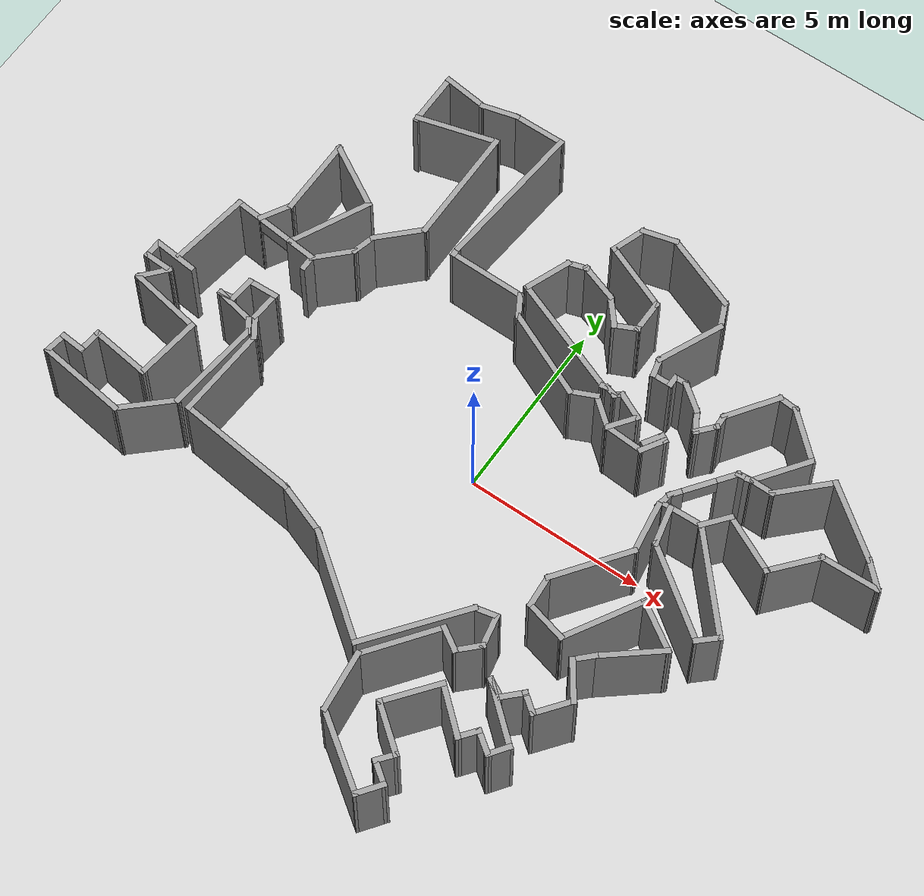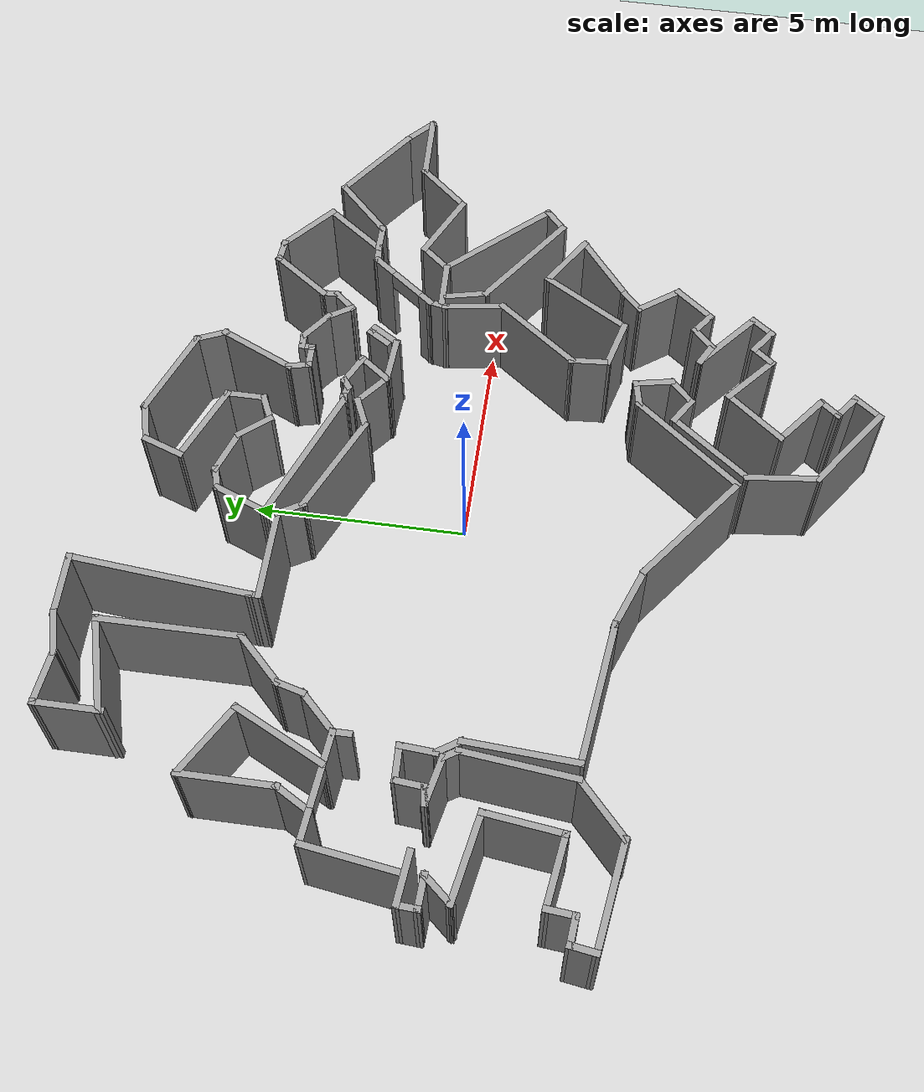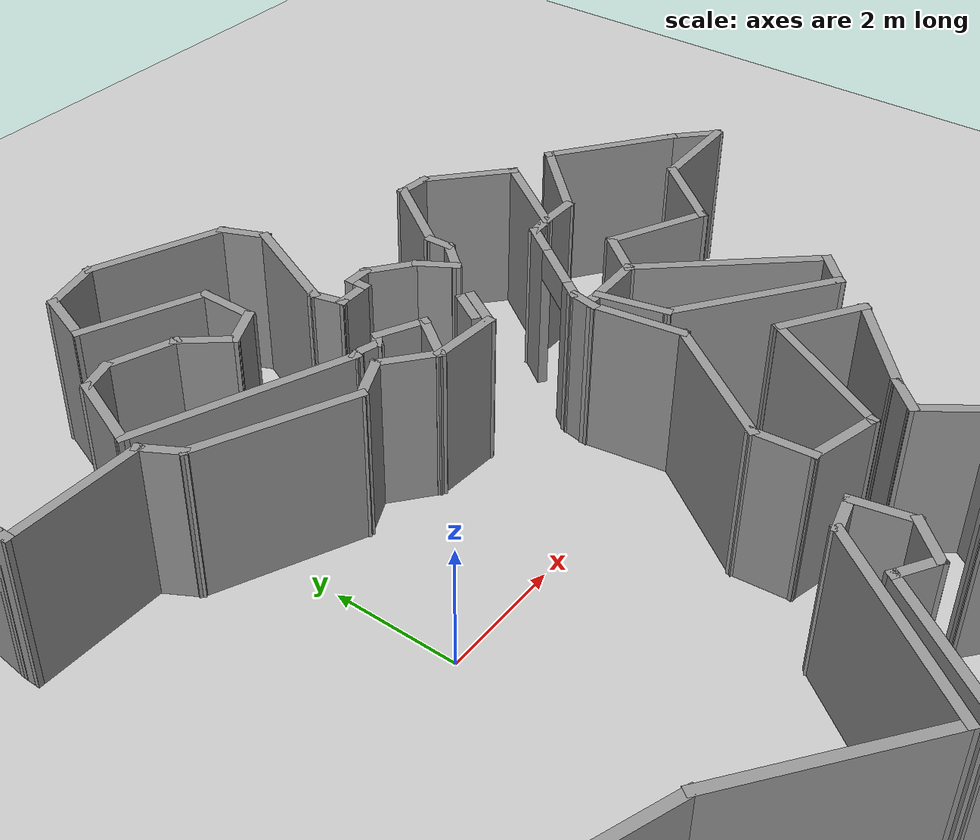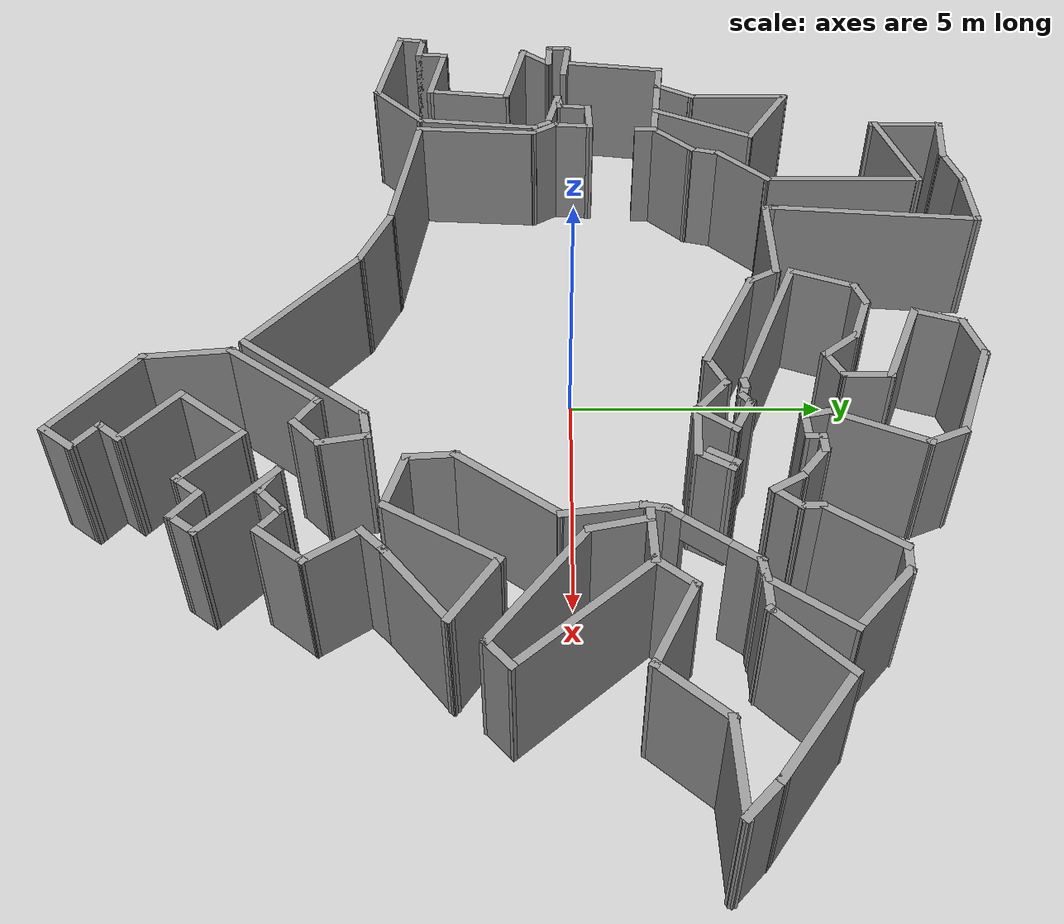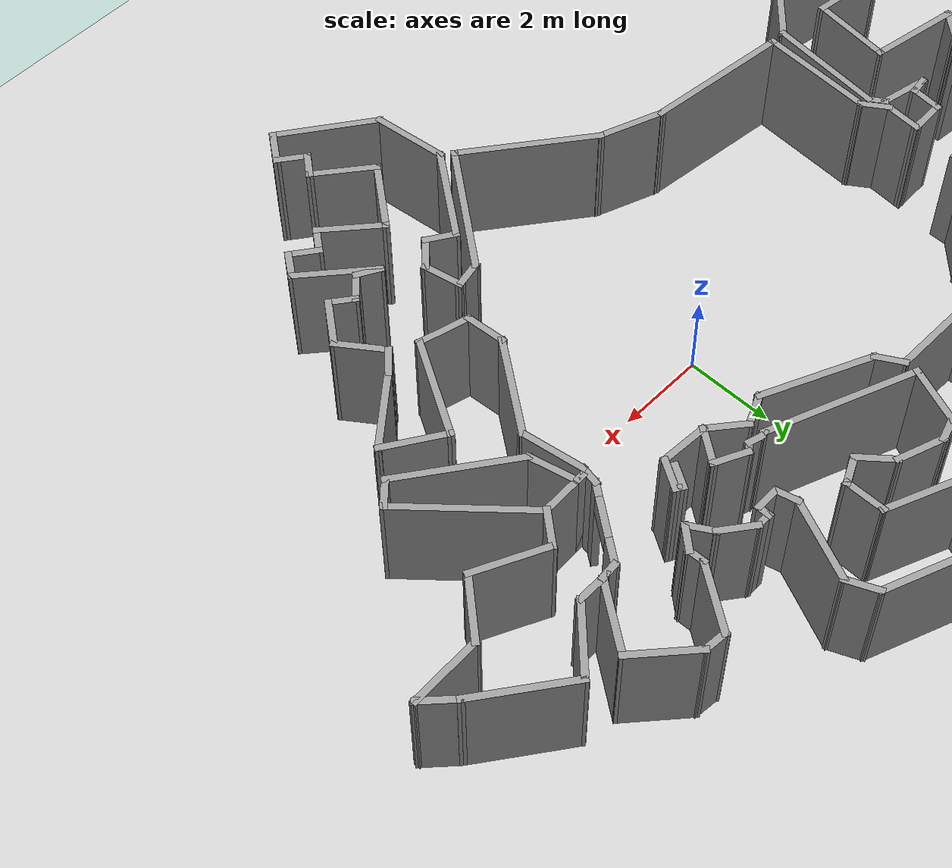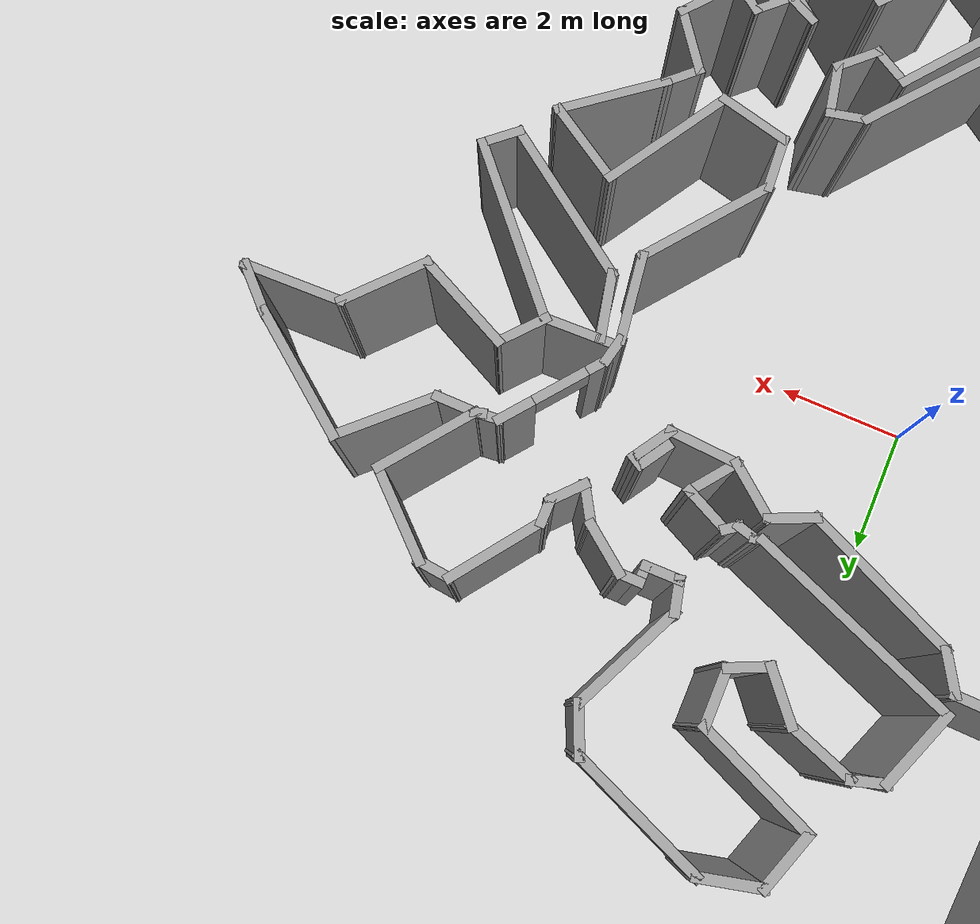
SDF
<sdf version="1.7">
 <world name="default">
  <light name="sun" type="directional">
   <pose>0 0 10 0 -0 0</pose>
   <diffuse>0.8 0.8 0.8 1</diffuse>
   <specular>0.2 0.2 0.2 1</specular>
   <attenuation>
    <range>1000</range>
    <constant>0.9</constant>
    <linear>0.01</linear>
    <quadratic>0.001</quadratic>
   </attenuation>
   <direction>-0.5 0.1 -0.9</direction>
   <spot><inner_angle>0</inner_angle><outer_angle>0</outer_angle><falloff>0</falloff></spot>
  </light>
  <model name="ground_plane">
   <static>1</static>
   <link name="link">
    <collision name="collision">
     <geometry><plane><normal>0 0 1</normal><size>100 100</size></plane></geometry>
     <surface><friction><ode><mu>100</mu><mu2>50</mu2></ode></friction></surface>
    </collision>
    <visual name="visual">
     <cast_shadows>0</cast_shadows>
     <geometry><plane><normal>0 0 1</normal><size>100 100</size></plane></geometry>
     <material>
      <script><uri>file://media/materials/scripts/gazebo.material</uri><name>Gazebo/Grey</name></script>
     </material>
    </visual>
   </link>
  </model>
  <gravity>0 0 -9.8</gravity>
  <magnetic_field>6e-06 2.3e-05 -4.2e-05</magnetic_field>
  <atmosphere type="adiabatic"/>
  <physics type="ode">
   <max_step_size>0.001</max_step_size>
   <real_time_factor>1</real_time_factor>
   <real_time_update_rate>1000</real_time_update_rate>
  </physics>
  <scene><ambient>0.4 0.4 0.4 1</ambient><background>0.7 0.7 0.7 1</background><shadows>1</shadows></scene>
  <audio><device>default</device></audio>
  <spherical_coordinates>
   <surface_model>EARTH_WGS84</surface_model>
   <latitude_deg>0</latitude_deg>
   <longitude_deg>0</longitude_deg>
   <elevation>0</elevation>
   <heading_deg>0</heading_deg>
  </spherical_coordinates>
  <model name="c82_house_gz">
   <pose>0.081452 -0.44571 0 0 -0 0</pose>
   <link name="Wall_0">
    <collision name="Wall_0_Collision">
     <geometry><box><size>1.61998 0.15 2.5</size></box></geometry>
     <pose>0 0 1.25 0 -0 0</pose>
    </collision>
    <visual name="Wall_0_Visual">
     <pose>0 0 1.25 0 -0 0</pose>
     <geometry><box><size>1.61998 0.15 2.5</size></box></geometry>
     <material>
      <script><uri>file://media/materials/scripts/gazebo.material</uri><name>Gazebo/Grey</name></script>
      <ambient>1 1 1 1</ambient>
     </material>
     <meta><layer>0</layer></meta>
    </visual>
    <pose>-6.59257 7.92893 0 0 -0 1.5708</pose>
   </link>
   <link name="Wall_1">
    <collision name="Wall_1_Collision">
     <geometry><box><size>1.33318 0.15 2.5</size></box></geometry>
     <pose>0 0 1.25 0 -0 0</pose>
    </collision>
    <visual name="Wall_1_Visual">
     <pose>0 0 1.25 0 -0 0</pose>
     <geometry><box><size>1.33318 0.15 2.5</size></box></geometry>
     <material>
      <script><uri>file://media/materials/scripts/gazebo.material</uri><name>Gazebo/Grey</name></script>
      <ambient>1 1 1 1</ambient>
     </material>
     <meta><layer>0</layer></meta>
    </visual>
    <pose>-6.00561 8.5898 0 0 -0 -0.125267</pose>
   </link>
   <link name="Wall_10">
    <collision name="Wall_10_Collision">
     <geometry><box><size>1.04168 0.15 2.5</size></box></geometry>
     <pose>0 0 1.25 0 -0 0</pose>
    </collision>
    <visual name="Wall_10_Visual">
     <pose>0 0 1.25 0 -0 0</pose>
     <geometry><box><size>1.04168 0.15 2.5</size></box></geometry>
     <material>
      <script><uri>file://media/materials/scripts/gazebo.material</uri><name>Gazebo/Grey</name></script>
      <ambient>1 1 1 1</ambient>
     </material>
     <meta><layer>0</layer></meta>
    </visual>
    <pose>2.08465 2.90774 0 0 -0 -0.685729</pose>
   </link>
   <link name="Wall_100">
    <collision name="Wall_100_Collision">
     <geometry><box><size>0.752581 0.15 2.5</size></box></geometry>
     <pose>0 0 1.25 0 -0 0</pose>
    </collision>
    <visual name="Wall_100_Visual">
     <pose>0 0 1.25 0 -0 0</pose>
     <geometry><box><size>0.752581 0.15 2.5</size></box></geometry>
     <material>
      <script><uri>file://media/materials/scripts/gazebo.material</uri><name>Gazebo/Grey</name></script>
      <ambient>1 1 1 1</ambient>
     </material>
     <meta><layer>0</layer></meta>
    </visual>
    <pose>-9.53018 -2.82113 0 0 -0 1.48014</pose>
   </link>
   <link name="Wall_101">
    <collision name="Wall_101_Collision">
     <geometry><box><size>1.74708 0.15 2.5</size></box></geometry>
     <pose>0 0 1.25 0 -0 0</pose>
    </collision>
    <visual name="Wall_101_Visual">
     <pose>0 0 1.25 0 -0 0</pose>
     <geometry><box><size>1.74708 0.15 2.5</size></box></geometry>
     <material>
      <script><uri>file://media/materials/scripts/gazebo.material</uri><name>Gazebo/Grey</name></script>
      <ambient>1 1 1 1</ambient>
     </material>
     <meta><layer>0</layer></meta>
    </visual>
    <pose>-8.71186 -2.63019 0 0 -0 -0.137066</pose>
   </link>
   <link name="Wall_102">
    <collision name="Wall_102_Collision">
     <geometry><box><size>1.90935 0.15 2.5</size></box></geometry>
     <pose>0 0 1.25 0 -0 0</pose>
    </collision>
    <visual name="Wall_102_Visual">
     <pose>0 0 1.25 0 -0 0</pose>
     <geometry><box><size>1.90935 0.15 2.5</size></box></geometry>
     <material>
      <script><uri>file://media/materials/scripts/gazebo.material</uri><name>Gazebo/Grey</name></script>
      <ambient>1 1 1 1</ambient>
     </material>
     <meta><layer>0</layer></meta>
    </visual>
    <pose>-7.8117 -1.86642 0 0 -0 1.44644</pose>
   </link>
   <link name="Wall_103">
    <collision name="Wall_103_Collision">
     <geometry><box><size>2.14574 0.15 2.5</size></box></geometry>
     <pose>0 0 1.25 0 -0 0</pose>
    </collision>
    <visual name="Wall_103_Visual">
     <pose>0 0 1.25 0 -0 0</pose>
     <geometry><box><size>2.14574 0.15 2.5</size></box></geometry>
     <material>
      <script><uri>file://media/materials/scripts/gazebo.material</uri><name>Gazebo/Grey</name></script>
      <ambient>1 1 1 1</ambient>
     </material>
     <meta><layer>0</layer></meta>
    </visual>
    <pose>-8.68458 -0.816233 0 0 -0 2.96296</pose>
   </link>
   <link name="Wall_104">
    <collision name="Wall_104_Collision">
     <geometry><box><size>0.942928 0.15 2.5</size></box></geometry>
     <pose>0 0 1.25 0 -0 0</pose>
    </collision>
    <visual name="Wall_104_Visual">
     <pose>0 0 1.25 0 -0 0</pose>
     <geometry><box><size>0.942928 0.15 2.5</size></box></geometry>
     <material>
      <script><uri>file://media/materials/scripts/gazebo.material</uri><name>Gazebo/Grey</name></script>
      <ambient>1 1 1 1</ambient>
     </material>
     <meta><layer>0</layer></meta>
    </visual>
    <pose>-9.40743 -0.338876 0 0 -0 0.858439</pose>
   </link>
   <link name="Wall_105">
    <collision name="Wall_105_Collision">
     <geometry><box><size>0.859741 0.15 2.5</size></box></geometry>
     <pose>0 0 1.25 0 -0 0</pose>
    </collision>
    <visual name="Wall_105_Visual">
     <pose>0 0 1.25 0 -0 0</pose>
     <geometry><box><size>0.859741 0.15 2.5</size></box></geometry>
     <material>
      <script><uri>file://media/materials/scripts/gazebo.material</uri><name>Gazebo/Grey</name></script>
      <ambient>1 1 1 1</ambient>
     </material>
     <meta><layer>0</layer></meta>
    </visual>
    <pose>-9.50291 -0.025184 0 0 -0 3.10315</pose>
   </link>
   <link name="Wall_106">
    <collision name="Wall_106_Collision">
     <geometry><box><size>0.587293 0.15 2.5</size></box></geometry>
     <pose>0 0 1.25 0 -0 0</pose>
    </collision>
    <visual name="Wall_106_Visual">
     <pose>0 0 1.25 0 -0 0</pose>
     <geometry><box><size>0.587293 0.15 2.5</size></box></geometry>
     <material>
      <script><uri>file://media/materials/scripts/gazebo.material</uri><name>Gazebo/Grey</name></script>
      <ambient>1 1 1 1</ambient>
     </material>
     <meta><layer>0</layer></meta>
    </visual>
    <pose>-9.84388 0.206675 0 0 -0 1.50838</pose>
   </link>
   <link name="Wall_107">
    <collision name="Wall_107_Collision">
     <geometry><box><size>1.27369 0.15 2.5</size></box></geometry>
     <pose>0 0 1.25 0 -0 0</pose>
    </collision>
    <visual name="Wall_107_Visual">
     <pose>0 0 1.25 0 -0 0</pose>
     <geometry><box><size>1.27369 0.15 2.5</size></box></geometry>
     <material>
      <script><uri>file://media/materials/scripts/gazebo.material</uri><name>Gazebo/Grey</name></script>
      <ambient>1 1 1 1</ambient>
     </material>
     <meta><layer>0</layer></meta>
    </visual>
    <pose>-9.27105 0.370341 0 0 -0 -0.097253</pose>
   </link>
   <link name="Wall_11">
    <collision name="Wall_11_Collision">
     <geometry><box><size>1.18708 0.15 2.5</size></box></geometry>
     <pose>0 0 1.25 0 -0 0</pose>
    </collision>
    <visual name="Wall_11_Visual">
     <pose>0 0 1.25 0 -0 0</pose>
     <geometry><box><size>1.18708 0.15 2.5</size></box></geometry>
     <material>
      <script><uri>file://media/materials/scripts/gazebo.material</uri><name>Gazebo/Grey</name></script>
      <ambient>1 1 1 1</ambient>
     </material>
     <meta><layer>0</layer></meta>
    </visual>
    <pose>2.9473 2.59405 0 0 -0 -0.060532</pose>
   </link>
   <link name="Wall_110">
    <collision name="Wall_110_Collision">
     <geometry><box><size>2.30192 0.15 2.5</size></box></geometry>
     <pose>0 0 1.25 0 -0 0</pose>
    </collision>
    <visual name="Wall_110_Visual">
     <pose>0 0 1.25 0 -0 0</pose>
     <geometry><box><size>2.30192 0.15 2.5</size></box></geometry>
     <material>
      <script><uri>file://media/materials/scripts/gazebo.material</uri><name>Gazebo/Grey</name></script>
      <ambient>1 1 1 1</ambient>
     </material>
     <meta><layer>0</layer></meta>
    </visual>
    <pose>-9.01638 1.49172 0 0 -0 1.42533</pose>
   </link>
   <link name="Wall_111">
    <pose>-7.6263 2.43426 0 0 -0 -0.098581</pose>
    <visual name="Wall_111_Visual_0">
     <pose>-0.88941 0 1.25 0 -0 0</pose>
     <geometry><box><size>0.851464 0.15 2.5</size></box></geometry>
     <material>
      <script><uri>file://media/materials/scripts/gazebo.material</uri><name>Gazebo/Grey</name></script>
      <ambient>1 1 1 1</ambient>
     </material>
     <meta><layer>0</layer></meta>
    </visual>
    <collision name="Wall_111_Collision_0">
     <geometry><box><size>0.851464 0.15 2.5</size></box></geometry>
     <pose>-0.88941 0 1.25 0 -0 0</pose>
    </collision>
    <visual name="Wall_111_Visual_1">
     <pose>0.875732 0 1.25 0 -0 0</pose>
     <geometry><box><size>0.87882 0.15 2.5</size></box></geometry>
     <material>
      <script><uri>file://media/materials/scripts/gazebo.material</uri><name>Gazebo/Grey</name></script>
      <ambient>1 1 1 1</ambient>
     </material>
     <meta><layer>0</layer></meta>
    </visual>
    <collision name="Wall_111_Collision_1">
     <geometry><box><size>0.87882 0.15 2.5</size></box></geometry>
     <pose>0.875732 0 1.25 0 -0 0</pose>
    </collision>
    <visual name="Wall_111_Visual_2">
     <pose>-0.013678 0 2.25 0 -0 0</pose>
     <geometry><box><size>0.9 0.15 0.5</size></box></geometry>
     <material>
      <script><uri>file://media/materials/scripts/gazebo.material</uri><name>Gazebo/Grey</name></script>
      <ambient>1 1 1 1</ambient>
     </material>
     <meta><layer>0</layer></meta>
    </visual>
    <collision name="Wall_111_Collision_2">
     <geometry><box><size>0.9 0.15 0.5</size></box></geometry>
     <pose>-0.013678 0 2.25 0 -0 0</pose>
    </collision>
   </link>
   <link name="Wall_112">
    <collision name="Wall_112_Collision">
     <geometry><box><size>0.5 0.15 2.5</size></box></geometry>
     <pose>0 0 1.25 0 -0 0</pose>
    </collision>
    <visual name="Wall_112_Visual">
     <pose>0 0 1.25 0 -0 0</pose>
     <geometry><box><size>0.5 0.15 2.5</size></box></geometry>
     <material>
      <script><uri>file://media/materials/scripts/gazebo.material</uri><name>Gazebo/Grey</name></script>
      <ambient>1 1 1 1</ambient>
     </material>
     <meta><layer>0</layer></meta>
    </visual>
    <pose>-6.39218 2.1372 0 0 -0 -1.5708</pose>
   </link>
   <link name="Wall_114">
    <collision name="Wall_114_Collision">
     <geometry><box><size>1.25 0.15 2.5</size></box></geometry>
     <pose>0 0 1.25 0 -0 0</pose>
    </collision>
    <visual name="Wall_114_Visual">
     <pose>0 0 1.25 0 -0 0</pose>
     <geometry><box><size>1.25 0.15 2.5</size></box></geometry>
     <material>
      <script><uri>file://media/materials/scripts/gazebo.material</uri><name>Gazebo/Grey</name></script>
      <ambient>1 1 1 1</ambient>
     </material>
     <meta><layer>0</layer></meta>
    </visual>
    <pose>-6.00327 2.70111 0 0 -0 0.785398</pose>
   </link>
   <link name="Wall_115">
    <collision name="Wall_115_Collision">
     <geometry><box><size>0.75 0.15 2.5</size></box></geometry>
     <pose>0 0 1.25 0 -0 0</pose>
    </collision>
    <visual name="Wall_115_Visual">
     <pose>0 0 1.25 0 -0 0</pose>
     <geometry><box><size>0.75 0.15 2.5</size></box></geometry>
     <material>
      <script><uri>file://media/materials/scripts/gazebo.material</uri><name>Gazebo/Grey</name></script>
      <ambient>1 1 1 1</ambient>
     </material>
     <meta><layer>0</layer></meta>
    </visual>
    <pose>-5.53671 3.3798 0 0 -0 1.309</pose>
   </link>
   <link name="Wall_116">
    <collision name="Wall_116_Collision">
     <geometry><box><size>1.5 0.15 2.5</size></box></geometry>
     <pose>0 0 1.25 0 -0 0</pose>
    </collision>
    <visual name="Wall_116_Visual">
     <pose>0 0 1.25 0 -0 0</pose>
     <geometry><box><size>1.5 0.15 2.5</size></box></geometry>
     <material>
      <script><uri>file://media/materials/scripts/gazebo.material</uri><name>Gazebo/Grey</name></script>
      <ambient>1 1 1 1</ambient>
     </material>
     <meta><layer>0</layer></meta>
    </visual>
    <pose>-4.98177 4.14687 0 0 -0 0.785398</pose>
   </link>
   <link name="Wall_117">
    <collision name="Wall_117_Collision">
     <geometry><box><size>3.34723 0.15 2.5</size></box></geometry>
     <pose>0 0 1.25 0 -0 0</pose>
    </collision>
    <visual name="Wall_117_Visual">
     <pose>0 0 1.25 0 -0 0</pose>
     <geometry><box><size>3.34723 0.15 2.5</size></box></geometry>
     <material>
      <script><uri>file://media/materials/scripts/gazebo.material</uri><name>Gazebo/Grey</name></script>
      <ambient>1 1 1 1</ambient>
     </material>
     <meta><layer>0</layer></meta>
    </visual>
    <pose>-4.50946 6.22253 0 0 -0 1.57392</pose>
   </link>
   <link name="Wall_118">
    <collision name="Wall_118_Collision">
     <geometry><box><size>2.31356 0.15 2.5</size></box></geometry>
     <pose>0 0 1.25 0 -0 0</pose>
    </collision>
    <visual name="Wall_118_Visual">
     <pose>0 0 1.25 0 -0 0</pose>
     <geometry><box><size>2.31356 0.15 2.5</size></box></geometry>
     <material>
      <script><uri>file://media/materials/scripts/gazebo.material</uri><name>Gazebo/Grey</name></script>
      <ambient>1 1 1 1</ambient>
     </material>
     <meta><layer>0</layer></meta>
    </visual>
    <pose>-5.55812 7.53625 0 0 -0 -2.87534</pose>
   </link>
   <link name="Wall_12">
    <collision name="Wall_12_Collision">
     <geometry><box><size>0.811734 0.15 2.5</size></box></geometry>
     <pose>0 0 1.25 0 -0 0</pose>
    </collision>
    <visual name="Wall_12_Visual">
     <pose>0 0 1.25 0 -0 0</pose>
     <geometry><box><size>0.811734 0.15 2.5</size></box></geometry>
     <material>
      <script><uri>file://media/materials/scripts/gazebo.material</uri><name>Gazebo/Grey</name></script>
      <ambient>1 1 1 1</ambient>
     </material>
     <meta><layer>0</layer></meta>
    </visual>
    <pose>3.63743 2.84501 0 0 -0 1.02225</pose>
   </link>
   <link name="Wall_120">
    <collision name="Wall_120_Collision">
     <geometry><box><size>0.505966 0.15 2.5</size></box></geometry>
     <pose>0 0 1.25 0 -0 0</pose>
    </collision>
    <visual name="Wall_120_Visual">
     <pose>0 0 1.25 0 -0 0</pose>
     <geometry><box><size>0.505966 0.15 2.5</size></box></geometry>
     <material>
      <script><uri>file://media/materials/scripts/gazebo.material</uri><name>Gazebo/Grey</name></script>
      <ambient>1 1 1 1</ambient>
     </material>
     <meta><layer>0</layer></meta>
    </visual>
    <pose>5.9717 3.41398 0 0 -0 0.104884</pose>
   </link>
   <link name="Wall_122">
    <collision name="Wall_122_Collision">
     <geometry><box><size>0.75 0.15 2.5</size></box></geometry>
     <pose>0 0 1.25 0 -0 0</pose>
    </collision>
    <visual name="Wall_122_Visual">
     <pose>0 0 1.25 0 -0 0</pose>
     <geometry><box><size>0.75 0.15 2.5</size></box></geometry>
     <material>
      <script><uri>file://media/materials/scripts/gazebo.material</uri><name>Gazebo/Grey</name></script>
      <ambient>1 1 1 1</ambient>
     </material>
     <meta><layer>0</layer></meta>
    </visual>
    <pose>6.4487 3.43261 0 0 -0 0</pose>
   </link>
   <link name="Wall_123">
    <collision name="Wall_123_Collision">
     <geometry><box><size>1.75 0.15 2.5</size></box></geometry>
     <pose>0 0 1.25 0 -0 0</pose>
    </collision>
    <visual name="Wall_123_Visual">
     <pose>0 0 1.25 0 -0 0</pose>
     <geometry><box><size>1.75 0.15 2.5</size></box></geometry>
     <material>
      <script><uri>file://media/materials/scripts/gazebo.material</uri><name>Gazebo/Grey</name></script>
      <ambient>1 1 1 1</ambient>
     </material>
     <meta><layer>0</layer></meta>
    </visual>
    <pose>7.31439 3.9983 0 0 -0 0.785398</pose>
   </link>
   <link name="Wall_124">
    <collision name="Wall_124_Collision">
     <geometry><box><size>2.34246 0.15 2.5</size></box></geometry>
     <pose>0 0 1.25 0 -0 0</pose>
    </collision>
    <visual name="Wall_124_Visual">
     <pose>0 0 1.25 0 -0 0</pose>
     <geometry><box><size>2.34246 0.15 2.5</size></box></geometry>
     <material>
      <script><uri>file://media/materials/scripts/gazebo.material</uri><name>Gazebo/Grey</name></script>
      <ambient>1 1 1 1</ambient>
     </material>
     <meta><layer>0</layer></meta>
    </visual>
    <pose>8.76248 3.91353 0 0 -0 -0.635221</pose>
   </link>
   <link name="Wall_125">
    <collision name="Wall_125_Collision">
     <geometry><box><size>0.939842 0.15 2.5</size></box></geometry>
     <pose>0 0 1.25 0 -0 0</pose>
    </collision>
    <visual name="Wall_125_Visual">
     <pose>0 0 1.25 0 -0 0</pose>
     <geometry><box><size>0.939842 0.15 2.5</size></box></geometry>
     <material>
      <script><uri>file://media/materials/scripts/gazebo.material</uri><name>Gazebo/Grey</name></script>
      <ambient>1 1 1 1</ambient>
     </material>
     <meta><layer>0</layer></meta>
    </visual>
    <pose>9.93178 2.99168 0 0 -0 -0.757628</pose>
   </link>
   <link name="Wall_126">
    <collision name="Wall_126_Collision">
     <geometry><box><size>1.70149 0.15 2.5</size></box></geometry>
     <pose>0 0 1.25 0 -0 0</pose>
    </collision>
    <visual name="Wall_126_Visual">
     <pose>0 0 1.25 0 -0 0</pose>
     <geometry><box><size>1.70149 0.15 2.5</size></box></geometry>
     <material>
      <script><uri>file://media/materials/scripts/gazebo.material</uri><name>Gazebo/Grey</name></script>
      <ambient>1 1 1 1</ambient>
     </material>
     <meta><layer>0</layer></meta>
    </visual>
    <pose>9.44327 2.69703 0 0 -0 -3.1116</pose>
   </link>
   <link name="Wall_127">
    <collision name="Wall_127_Collision">
     <geometry><box><size>1.5579 0.15 2.5</size></box></geometry>
     <pose>0 0 1.25 0 -0 0</pose>
    </collision>
    <visual name="Wall_127_Visual">
     <pose>0 0 1.25 0 -0 0</pose>
     <geometry><box><size>1.5579 0.15 2.5</size></box></geometry>
     <material>
      <script><uri>file://media/materials/scripts/gazebo.material</uri><name>Gazebo/Grey</name></script>
      <ambient>1 1 1 1</ambient>
     </material>
     <meta><layer>0</layer></meta>
    </visual>
    <pose>8.21039 2.13875 0 0 -0 -2.27823</pose>
   </link>
   <link name="Wall_128">
    <collision name="Wall_128_Collision">
     <geometry><box><size>1.78688 0.15 2.5</size></box></geometry>
     <pose>0 0 1.25 0 -0 0</pose>
    </collision>
    <visual name="Wall_128_Visual">
     <pose>0 0 1.25 0 -0 0</pose>
     <geometry><box><size>1.78688 0.15 2.5</size></box></geometry>
     <material>
      <script><uri>file://media/materials/scripts/gazebo.material</uri><name>Gazebo/Grey</name></script>
      <ambient>1 1 1 1</ambient>
     </material>
     <meta><layer>0</layer></meta>
    </visual>
    <pose>7.01628 1.9604 0 0 -0 2.69066</pose>
   </link>
   <link name="Wall_129">
    <collision name="Wall_129_Collision">
     <geometry><box><size>0.932346 0.15 2.5</size></box></geometry>
     <pose>0 0 1.25 0 -0 0</pose>
    </collision>
    <visual name="Wall_129_Visual">
     <pose>0 0 1.25 0 -0 0</pose>
     <geometry><box><size>0.932346 0.15 2.5</size></box></geometry>
     <material>
      <script><uri>file://media/materials/scripts/gazebo.material</uri><name>Gazebo/Grey</name></script>
      <ambient>1 1 1 1</ambient>
     </material>
     <meta><layer>0</layer></meta>
    </visual>
    <pose>6.03152 2.01468 0 0 -0 -2.25792</pose>
   </link>
   <link name="Wall_130">
    <pose>5.27938 1.69677 0 0 -0 -3.11083</pose>
    <visual name="Wall_130_Visual_0">
     <pose>0 0 1.25 0 -0 0</pose>
     <geometry><box><size>1.1585 0.15 2.5</size></box></geometry>
     <material>
      <script><uri>file://media/materials/scripts/gazebo.material</uri><name>Gazebo/Grey</name></script>
      <ambient>1 1 1 1</ambient>
     </material>
     <meta><layer>0</layer></meta>
    </visual>
    <collision name="Wall_130_Collision_0">
     <geometry><box><size>1.1585 0.15 2.5</size></box></geometry>
     <pose>0 0 1.25 0 -0 0</pose>
    </collision>
    <visual name="Wall_130_Visual_1">
     <pose>0.446838 0 1.25 0 -0 0</pose>
     <geometry><box><size>0.264818 0.15 2.5</size></box></geometry>
     <material>
      <script><uri>file://media/materials/scripts/gazebo.material</uri><name>Gazebo/Grey</name></script>
      <ambient>1 1 1 1</ambient>
     </material>
     <meta><layer>0</layer></meta>
    </visual>
    <collision name="Wall_130_Collision_1">
     <geometry><box><size>0.264818 0.15 2.5</size></box></geometry>
     <pose>0.446838 0 1.25 0 -0 0</pose>
    </collision>
   </link>
   <link name="Wall_132">
    <collision name="Wall_132_Collision">
     <geometry><box><size>1 0.15 2.5</size></box></geometry>
     <pose>0 0 1.25 0 -0 0</pose>
    </collision>
    <visual name="Wall_132_Visual">
     <pose>0 0 1.25 0 -0 0</pose>
     <geometry><box><size>1 0.15 2.5</size></box></geometry>
     <material>
      <script><uri>file://media/materials/scripts/gazebo.material</uri><name>Gazebo/Grey</name></script>
      <ambient>1 1 1 1</ambient>
     </material>
     <meta><layer>0</layer></meta>
    </visual>
    <pose>-7.93835 2.87124 0 0 -0 1.0472</pose>
   </link>
   <link name="Wall_133">
    <collision name="Wall_133_Collision">
     <geometry><box><size>2.25 0.15 2.5</size></box></geometry>
     <pose>0 0 1.25 0 -0 0</pose>
    </collision>
    <visual name="Wall_133_Visual">
     <pose>0 0 1.25 0 -0 0</pose>
     <geometry><box><size>2.25 0.15 2.5</size></box></geometry>
     <material>
      <script><uri>file://media/materials/scripts/gazebo.material</uri><name>Gazebo/Grey</name></script>
      <ambient>1 1 1 1</ambient>
     </material>
     <meta><layer>0</layer></meta>
    </visual>
    <pose>-7.72585 4.2893 0 0 -0 1.5708</pose>
   </link>
   <link name="Wall_134">
    <collision name="Wall_134_Collision">
     <geometry><box><size>2 0.15 2.5</size></box></geometry>
     <pose>0 0 1.25 0 -0 0</pose>
    </collision>
    <visual name="Wall_134_Visual">
     <pose>0 0 1.25 0 -0 0</pose>
     <geometry><box><size>2 0.15 2.5</size></box></geometry>
     <material>
      <script><uri>file://media/materials/scripts/gazebo.material</uri><name>Gazebo/Grey</name></script>
      <ambient>1 1 1 1</ambient>
     </material>
     <meta><layer>0</layer></meta>
    </visual>
    <pose>-6.92478 4.87681 0 0 -0 -0.523599</pose>
   </link>
   <link name="Wall_135">
    <collision name="Wall_135_Collision">
     <geometry><box><size>2.38602 0.15 2.5</size></box></geometry>
     <pose>0 0 1.25 0 -0 0</pose>
    </collision>
    <visual name="Wall_135_Visual">
     <pose>0 0 1.25 0 -0 0</pose>
     <geometry><box><size>2.38602 0.15 2.5</size></box></geometry>
     <material>
      <script><uri>file://media/materials/scripts/gazebo.material</uri><name>Gazebo/Grey</name></script>
      <ambient>1 1 1 1</ambient>
     </material>
     <meta><layer>0</layer></meta>
    </visual>
    <pose>-6.6181 3.41155 0 0 -0 -2.02886</pose>
   </link>
   <link name="Wall_139">
    <collision name="Wall_139_Collision">
     <geometry><box><size>1.17812 0.15 2.5</size></box></geometry>
     <pose>0 0 1.25 0 -0 0</pose>
    </collision>
    <visual name="Wall_139_Visual">
     <pose>0 0 1.25 0 -0 0</pose>
     <geometry><box><size>1.17812 0.15 2.5</size></box></geometry>
     <material>
      <script><uri>file://media/materials/scripts/gazebo.material</uri><name>Gazebo/Grey</name></script>
      <ambient>1 1 1 1</ambient>
     </material>
     <meta><layer>0</layer></meta>
    </visual>
    <pose>5.0439 1.17068 0 0 -0 -1.34464</pose>
   </link>
   <link name="Wall_14">
    <collision name="Wall_14_Collision">
     <geometry><box><size>0.301971 0.15 2.5</size></box></geometry>
     <pose>0 0 1.25 0 -0 0</pose>
    </collision>
    <visual name="Wall_14_Visual">
     <pose>0 0 1.25 0 -0 0</pose>
     <geometry><box><size>0.301971 0.15 2.5</size></box></geometry>
     <material>
      <script><uri>file://media/materials/scripts/gazebo.material</uri><name>Gazebo/Grey</name></script>
      <ambient>1 1 1 1</ambient>
     </material>
     <meta><layer>0</layer></meta>
    </visual>
    <pose>3.74405 3.16515 0 0 -0 2.62064</pose>
   </link>
   <link name="Wall_140">
    <collision name="Wall_140_Collision">
     <geometry><box><size>2.8619 0.15 2.5</size></box></geometry>
     <pose>0 0 1.25 0 -0 0</pose>
    </collision>
    <visual name="Wall_140_Visual">
     <pose>0 0 1.25 0 -0 0</pose>
     <geometry><box><size>2.8619 0.15 2.5</size></box></geometry>
     <material>
      <script><uri>file://media/materials/scripts/gazebo.material</uri><name>Gazebo/Grey</name></script>
      <ambient>1 1 1 1</ambient>
     </material>
     <meta><layer>0</layer></meta>
    </visual>
    <pose>6.25864 -0.123861 0 0 -0 -0.62519</pose>
   </link>
   <link name="Wall_141">
    <collision name="Wall_141_Collision">
     <geometry><box><size>0.739888 0.15 2.5</size></box></geometry>
     <pose>0 0 1.25 0 -0 0</pose>
    </collision>
    <visual name="Wall_141_Visual">
     <pose>0 0 1.25 0 -0 0</pose>
     <geometry><box><size>0.739888 0.15 2.5</size></box></geometry>
     <material>
      <script><uri>file://media/materials/scripts/gazebo.material</uri><name>Gazebo/Grey</name></script>
      <ambient>1 1 1 1</ambient>
     </material>
     <meta><layer>0</layer></meta>
    </visual>
    <pose>7.57535 -0.717932 0 0 -0 0.742871</pose>
   </link>
   <link name="Wall_142">
    <collision name="Wall_142_Collision">
     <geometry><box><size>3.10789 0.15 2.5</size></box></geometry>
     <pose>0 0 1.25 0 -0 0</pose>
    </collision>
    <visual name="Wall_142_Visual">
     <pose>0 0 1.25 0 -0 0</pose>
     <geometry><box><size>3.10789 0.15 2.5</size></box></geometry>
     <material>
      <script><uri>file://media/materials/scripts/gazebo.material</uri><name>Gazebo/Grey</name></script>
      <ambient>1 1 1 1</ambient>
     </material>
     <meta><layer>0</layer></meta>
    </visual>
    <pose>6.80838 0.585478 0 0 -0 2.29893</pose>
   </link>
   <link name="Wall_15">
    <collision name="Wall_15_Collision">
     <geometry><box><size>0.642437 0.15 2.5</size></box></geometry>
     <pose>0 0 1.25 0 -0 0</pose>
    </collision>
    <visual name="Wall_15_Visual">
     <pose>0 0 1.25 0 -0 0</pose>
     <geometry><box><size>0.642437 0.15 2.5</size></box></geometry>
     <material>
      <script><uri>file://media/materials/scripts/gazebo.material</uri><name>Gazebo/Grey</name></script>
      <ambient>1 1 1 1</ambient>
     </material>
     <meta><layer>0</layer></meta>
    </visual>
    <pose>3.54996 2.99274 0 0 -0 -2.11836</pose>
   </link>
   <link name="Wall_17">
    <collision name="Wall_17_Collision">
     <geometry><box><size>0.942747 0.15 2.5</size></box></geometry>
     <pose>0 0 1.25 0 -0 0</pose>
    </collision>
    <visual name="Wall_17_Visual">
     <pose>0 0 1.25 0 -0 0</pose>
     <geometry><box><size>0.942747 0.15 2.5</size></box></geometry>
     <material>
      <script><uri>file://media/materials/scripts/gazebo.material</uri><name>Gazebo/Grey</name></script>
      <ambient>1 1 1 1</ambient>
     </material>
     <meta><layer>0</layer></meta>
    </visual>
    <pose>2.66425 2.94496 0 0 -0 0.937612</pose>
   </link>
   <link name="Wall_18">
    <collision name="Wall_18_Collision">
     <geometry><box><size>0.879234 0.15 2.5</size></box></geometry>
     <pose>0 0 1.25 0 -0 0</pose>
    </collision>
    <visual name="Wall_18_Visual">
     <pose>0 0 1.25 0 -0 0</pose>
     <geometry><box><size>0.879234 0.15 2.5</size></box></geometry>
     <material>
      <script><uri>file://media/materials/scripts/gazebo.material</uri><name>Gazebo/Grey</name></script>
      <ambient>1 1 1 1</ambient>
     </material>
     <meta><layer>0</layer></meta>
    </visual>
    <pose>2.57064 3.42344 0 0 -0 2.69052</pose>
   </link>
   <link name="Wall_19">
    <collision name="Wall_19_Collision">
     <geometry><box><size>0.355093 0.15 2.5</size></box></geometry>
     <pose>0 0 1.25 0 -0 0</pose>
    </collision>
    <visual name="Wall_19_Visual">
     <pose>0 0 1.25 0 -0 0</pose>
     <geometry><box><size>0.355093 0.15 2.5</size></box></geometry>
     <material>
      <script><uri>file://media/materials/scripts/gazebo.material</uri><name>Gazebo/Grey</name></script>
      <ambient>1 1 1 1</ambient>
     </material>
     <meta><layer>0</layer></meta>
    </visual>
    <pose>2.16046 3.52086 0 0 -0 -2.49809</pose>
   </link>
   <link name="Wall_2">
    <collision name="Wall_2_Collision">
     <geometry><box><size>1.09275 0.15 2.5</size></box></geometry>
     <pose>0 0 1.25 0 -0 0</pose>
    </collision>
    <visual name="Wall_2_Visual">
     <pose>0 0 1.25 0 -0 0</pose>
     <geometry><box><size>1.09275 0.15 2.5</size></box></geometry>
     <material>
      <script><uri>file://media/materials/scripts/gazebo.material</uri><name>Gazebo/Grey</name></script>
      <ambient>1 1 1 1</ambient>
     </material>
     <meta><layer>0</layer></meta>
    </visual>
    <pose>-4.96213 8.63327 0 0 -0 0.25169</pose>
   </link>
   <link name="Wall_20">
    <collision name="Wall_20_Collision">
     <geometry><box><size>0.426115 0.15 2.5</size></box></geometry>
     <pose>0 0 1.25 0 -0 0</pose>
    </collision>
    <visual name="Wall_20_Visual">
     <pose>0 0 1.25 0 -0 0</pose>
     <geometry><box><size>0.426115 0.15 2.5</size></box></geometry>
     <material>
      <script><uri>file://media/materials/scripts/gazebo.material</uri><name>Gazebo/Grey</name></script>
      <ambient>1 1 1 1</ambient>
     </material>
     <meta><layer>0</layer></meta>
    </visual>
    <pose>1.94511 3.49522 0 0 -0 2.8786</pose>
   </link>
   <link name="Wall_21">
    <collision name="Wall_21_Collision">
     <geometry><box><size>0.26465 0.15 2.5</size></box></geometry>
     <pose>0 0 1.25 0 -0 0</pose>
    </collision>
    <visual name="Wall_21_Visual">
     <pose>0 0 1.25 0 -0 0</pose>
     <geometry><box><size>0.26465 0.15 2.5</size></box></geometry>
     <material>
      <script><uri>file://media/materials/scripts/gazebo.material</uri><name>Gazebo/Grey</name></script>
      <ambient>1 1 1 1</ambient>
     </material>
     <meta><layer>0</layer></meta>
    </visual>
    <pose>1.7554 3.52086 0 0 -0 -2.96174</pose>
   </link>
   <link name="Wall_22">
    <collision name="Wall_22_Collision">
     <geometry><box><size>3.51104 0.15 2.5</size></box></geometry>
     <pose>0 0 1.25 0 -0 0</pose>
    </collision>
    <visual name="Wall_22_Visual">
     <pose>0 0 1.25 0 -0 0</pose>
     <geometry><box><size>3.51104 0.15 2.5</size></box></geometry>
     <material>
      <script><uri>file://media/materials/scripts/gazebo.material</uri><name>Gazebo/Grey</name></script>
      <ambient>1 1 1 1</ambient>
     </material>
     <meta><layer>0</layer></meta>
    </visual>
    <pose>0.135165 4.12588 0 0 -0 2.76675</pose>
   </link>
   <link name="Wall_23">
    <collision name="Wall_23_Collision">
     <geometry><box><size>1.40681 0.15 2.5</size></box></geometry>
     <pose>0 0 1.25 0 -0 0</pose>
    </collision>
    <visual name="Wall_23_Visual">
     <pose>0 0 1.25 0 -0 0</pose>
     <geometry><box><size>1.40681 0.15 2.5</size></box></geometry>
     <material>
      <script><uri>file://media/materials/scripts/gazebo.material</uri><name>Gazebo/Grey</name></script>
      <ambient>1 1 1 1</ambient>
     </material>
     <meta><layer>0</layer></meta>
    </visual>
    <pose>-1.19794 5.32568 0 0 -0 1.19484</pose>
   </link>
   <link name="Wall_24">
    <collision name="Wall_24_Collision">
     <geometry><box><size>0.633276 0.15 2.5</size></box></geometry>
     <pose>0 0 1.25 0 -0 0</pose>
    </collision>
    <visual name="Wall_24_Visual">
     <pose>0 0 1.25 0 -0 0</pose>
     <geometry><box><size>0.633276 0.15 2.5</size></box></geometry>
     <material>
      <script><uri>file://media/materials/scripts/gazebo.material</uri><name>Gazebo/Grey</name></script>
      <ambient>1 1 1 1</ambient>
     </material>
     <meta><layer>0</layer></meta>
    </visual>
    <pose>-0.73648 5.98197 0 0 -0 0.301619</pose>
   </link>
   <link name="Wall_25">
    <collision name="Wall_25_Collision">
     <geometry><box><size>1.17161 0.15 2.5</size></box></geometry>
     <pose>0 0 1.25 0 -0 0</pose>
    </collision>
    <visual name="Wall_25_Visual">
     <pose>0 0 1.25 0 -0 0</pose>
     <geometry><box><size>1.17161 0.15 2.5</size></box></geometry>
     <material>
      <script><uri>file://media/materials/scripts/gazebo.material</uri><name>Gazebo/Grey</name></script>
      <ambient>1 1 1 1</ambient>
     </material>
     <meta><layer>0</layer></meta>
    </visual>
    <pose>-0.023782 5.88455 0 0 -0 -0.337622</pose>
   </link>
   <link name="Wall_26">
    <collision name="Wall_26_Collision">
     <geometry><box><size>0.965357 0.15 2.5</size></box></geometry>
     <pose>0 0 1.25 0 -0 0</pose>
    </collision>
    <visual name="Wall_26_Visual">
     <pose>0 0 1.25 0 -0 0</pose>
     <geometry><box><size>0.965357 0.15 2.5</size></box></geometry>
     <material>
      <script><uri>file://media/materials/scripts/gazebo.material</uri><name>Gazebo/Grey</name></script>
      <ambient>1 1 1 1</ambient>
     </material>
     <meta><layer>0</layer></meta>
    </visual>
    <pose>0.71968 5.40259 0 0 -0 -0.874448</pose>
   </link>
   <link name="Wall_27">
    <collision name="Wall_27_Collision">
     <geometry><box><size>0.750926 0.15 2.5</size></box></geometry>
     <pose>0 0 1.25 0 -0 0</pose>
    </collision>
    <visual name="Wall_27_Visual">
     <pose>0 0 1.25 0 -0 0</pose>
     <geometry><box><size>0.750926 0.15 2.5</size></box></geometry>
     <material>
      <script><uri>file://media/materials/scripts/gazebo.material</uri><name>Gazebo/Grey</name></script>
      <ambient>1 1 1 1</ambient>
     </material>
     <meta><layer>0</layer></meta>
    </visual>
    <pose>1.25292 5.218 0 0 -0 0.440751</pose>
   </link>
   <link name="Wall_29">
    <collision name="Wall_29_Collision">
     <geometry><box><size>1 0.15 2.5</size></box></geometry>
     <pose>0 0 1.25 0 -0 0</pose>
    </collision>
    <visual name="Wall_29_Visual">
     <pose>0 0 1.25 0 -0 0</pose>
     <geometry><box><size>1 0.15 2.5</size></box></geometry>
     <material>
      <script><uri>file://media/materials/scripts/gazebo.material</uri><name>Gazebo/Grey</name></script>
      <ambient>1 1 1 1</ambient>
     </material>
     <meta><layer>0</layer></meta>
    </visual>
    <pose>1.52467 5.77119 0 0 -0 1.5708</pose>
   </link>
   <link name="Wall_3">
    <collision name="Wall_3_Collision">
     <geometry><box><size>1.52394 0.15 2.5</size></box></geometry>
     <pose>0 0 1.25 0 -0 0</pose>
    </collision>
    <visual name="Wall_3_Visual">
     <pose>0 0 1.25 0 -0 0</pose>
     <geometry><box><size>1.52394 0.15 2.5</size></box></geometry>
     <material>
      <script><uri>file://media/materials/scripts/gazebo.material</uri><name>Gazebo/Grey</name></script>
      <ambient>1 1 1 1</ambient>
     </material>
     <meta><layer>0</layer></meta>
    </visual>
    <pose>-3.81865 8.75501 0 0 -0 0.006329</pose>
   </link>
   <link name="Wall_30">
    <collision name="Wall_30_Collision">
     <geometry><box><size>2.05668 0.15 2.5</size></box></geometry>
     <pose>0 0 1.25 0 -0 0</pose>
    </collision>
    <visual name="Wall_30_Visual">
     <pose>0 0 1.25 0 -0 0</pose>
     <geometry><box><size>2.05668 0.15 2.5</size></box></geometry>
     <material>
      <script><uri>file://media/materials/scripts/gazebo.material</uri><name>Gazebo/Grey</name></script>
      <ambient>1 1 1 1</ambient>
     </material>
     <meta><layer>0</layer></meta>
    </visual>
    <pose>0.64437 6.56215 0 0 -0 2.7476</pose>
   </link>
   <link name="Wall_31">
    <collision name="Wall_31_Collision">
     <geometry><box><size>1.05814 0.15 2.5</size></box></geometry>
     <pose>0 0 1.25 0 -0 0</pose>
    </collision>
    <visual name="Wall_31_Visual">
     <pose>0 0 1.25 0 -0 0</pose>
     <geometry><box><size>1.05814 0.15 2.5</size></box></geometry>
     <material>
      <script><uri>file://media/materials/scripts/gazebo.material</uri><name>Gazebo/Grey</name></script>
      <ambient>1 1 1 1</ambient>
     </material>
     <meta><layer>0</layer></meta>
    </visual>
    <pose>-0.084338 7.35613 0 0 -0 1.23041</pose>
   </link>
   <link name="Wall_32">
    <collision name="Wall_32_Collision">
     <geometry><box><size>1.04322 0.15 2.5</size></box></geometry>
     <pose>0 0 1.25 0 -0 0</pose>
    </collision>
    <visual name="Wall_32_Visual">
     <pose>0 0 1.25 0 -0 0</pose>
     <geometry><box><size>1.04322 0.15 2.5</size></box></geometry>
     <material>
      <script><uri>file://media/materials/scripts/gazebo.material</uri><name>Gazebo/Grey</name></script>
      <ambient>1 1 1 1</ambient>
     </material>
     <meta><layer>0</layer></meta>
    </visual>
    <pose>0.499731 7.89561 0 0 -0 0.252242</pose>
   </link>
   <link name="Wall_33">
    <collision name="Wall_33_Collision">
     <geometry><box><size>2.28774 0.15 2.5</size></box></geometry>
     <pose>0 0 1.25 0 -0 0</pose>
    </collision>
    <visual name="Wall_33_Visual">
     <pose>0 0 1.25 0 -0 0</pose>
     <geometry><box><size>2.28774 0.15 2.5</size></box></geometry>
     <material>
      <script><uri>file://media/materials/scripts/gazebo.material</uri><name>Gazebo/Grey</name></script>
      <ambient>1 1 1 1</ambient>
     </material>
     <meta><layer>0</layer></meta>
    </visual>
    <pose>1.92646 7.61472 0 0 -0 -0.375859</pose>
   </link>
   <link name="Wall_34">
    <collision name="Wall_34_Collision">
     <geometry><box><size>0.840829 0.15 2.5</size></box></geometry>
     <pose>0 0 1.25 0 -0 0</pose>
    </collision>
    <visual name="Wall_34_Visual">
     <pose>0 0 1.25 0 -0 0</pose>
     <geometry><box><size>0.840829 0.15 2.5</size></box></geometry>
     <material>
      <script><uri>file://media/materials/scripts/gazebo.material</uri><name>Gazebo/Grey</name></script>
      <ambient>1 1 1 1</ambient>
     </material>
     <meta><layer>0</layer></meta>
    </visual>
    <pose>3.05893 6.90582 0 0 -0 -1.15912</pose>
   </link>
   <link name="Wall_35">
    <collision name="Wall_35_Collision">
     <geometry><box><size>1.95808 0.15 2.5</size></box></geometry>
     <pose>0 0 1.25 0 -0 0</pose>
    </collision>
    <visual name="Wall_35_Visual">
     <pose>0 0 1.25 0 -0 0</pose>
     <geometry><box><size>1.95808 0.15 2.5</size></box></geometry>
     <material>
      <script><uri>file://media/materials/scripts/gazebo.material</uri><name>Gazebo/Grey</name></script>
      <ambient>1 1 1 1</ambient>
     </material>
     <meta><layer>0</layer></meta>
    </visual>
    <pose>2.82709 5.76443 0 0 -0 -1.99253</pose>
   </link>
   <link name="Wall_36">
    <collision name="Wall_36_Collision">
     <geometry><box><size>0.608515 0.15 2.5</size></box></geometry>
     <pose>0 0 1.25 0 -0 0</pose>
    </collision>
    <visual name="Wall_36_Visual">
     <pose>0 0 1.25 0 -0 0</pose>
     <geometry><box><size>0.608515 0.15 2.5</size></box></geometry>
     <material>
      <script><uri>file://media/materials/scripts/gazebo.material</uri><name>Gazebo/Grey</name></script>
      <ambient>1 1 1 1</ambient>
     </material>
     <meta><layer>0</layer></meta>
    </visual>
    <pose>2.51053 4.71667 0 0 -0 -1.33525</pose>
   </link>
   <link name="Wall_37">
    <collision name="Wall_37_Collision">
     <geometry><box><size>0.649436 0.15 2.5</size></box></geometry>
     <pose>0 0 1.25 0 -0 0</pose>
    </collision>
    <visual name="Wall_37_Visual">
     <pose>0 0 1.25 0 -0 0</pose>
     <geometry><box><size>0.649436 0.15 2.5</size></box></geometry>
     <material>
      <script><uri>file://media/materials/scripts/gazebo.material</uri><name>Gazebo/Grey</name></script>
      <ambient>1 1 1 1</ambient>
     </material>
     <meta><layer>0</layer></meta>
    </visual>
    <pose>2.81371 4.4982 0 0 -0 0.017855</pose>
   </link>
   <link name="Wall_38">
    <collision name="Wall_38_Collision">
     <geometry><box><size>0.390926 0.15 2.5</size></box></geometry>
     <pose>0 0 1.25 0 -0 0</pose>
    </collision>
    <visual name="Wall_38_Visual">
     <pose>0 0 1.25 0 -0 0</pose>
     <geometry><box><size>0.390926 0.15 2.5</size></box></geometry>
     <material>
      <script><uri>file://media/materials/scripts/gazebo.material</uri><name>Gazebo/Grey</name></script>
      <ambient>1 1 1 1</ambient>
     </material>
     <meta><layer>0</layer></meta>
    </visual>
    <pose>3.06339 4.62304 0 0 -0 1.5708</pose>
   </link>
   <link name="Wall_39">
    <collision name="Wall_39_Collision">
     <geometry><box><size>0.453705 0.15 2.5</size></box></geometry>
     <pose>0 0 1.25 0 -0 0</pose>
    </collision>
    <visual name="Wall_39_Visual">
     <pose>0 0 1.25 0 -0 0</pose>
     <geometry><box><size>0.453705 0.15 2.5</size></box></geometry>
     <material>
      <script><uri>file://media/materials/scripts/gazebo.material</uri><name>Gazebo/Grey</name></script>
      <ambient>1 1 1 1</ambient>
     </material>
     <meta><layer>0</layer></meta>
    </visual>
    <pose>3.21498 4.74342 0 0 -0 0</pose>
   </link>
   <link name="Wall_4">
    <collision name="Wall_4_Collision">
     <geometry><box><size>4.2619 0.15 2.5</size></box></geometry>
     <pose>0 0 1.25 0 -0 0</pose>
    </collision>
    <visual name="Wall_4_Visual">
     <pose>0 0 1.25 0 -0 0</pose>
     <geometry><box><size>4.2619 0.15 2.5</size></box></geometry>
     <material>
      <script><uri>file://media/materials/scripts/gazebo.material</uri><name>Gazebo/Grey</name></script>
      <ambient>1 1 1 1</ambient>
     </material>
     <meta><layer>0</layer></meta>
    </visual>
    <pose>-3.31431 6.71153 0 0 -0 -1.65973</pose>
   </link>
   <link name="Wall_40">
    <collision name="Wall_40_Collision">
     <geometry><box><size>0.932928 0.15 2.5</size></box></geometry>
     <pose>0 0 1.25 0 -0 0</pose>
    </collision>
    <visual name="Wall_40_Visual">
     <pose>0 0 1.25 0 -0 0</pose>
     <geometry><box><size>0.932928 0.15 2.5</size></box></geometry>
     <material>
      <script><uri>file://media/materials/scripts/gazebo.material</uri><name>Gazebo/Grey</name></script>
      <ambient>1 1 1 1</ambient>
     </material>
     <meta><layer>0</layer></meta>
    </visual>
    <pose>3.67867 4.50712 0 0 -0 -0.648057</pose>
   </link>
   <link name="Wall_41">
    <collision name="Wall_41_Collision">
     <geometry><box><size>0.734188 0.15 2.5</size></box></geometry>
     <pose>0 0 1.25 0 -0 0</pose>
    </collision>
    <visual name="Wall_41_Visual">
     <pose>0 0 1.25 0 -0 0</pose>
     <geometry><box><size>0.734188 0.15 2.5</size></box></geometry>
     <material>
      <script><uri>file://media/materials/scripts/gazebo.material</uri><name>Gazebo/Grey</name></script>
      <ambient>1 1 1 1</ambient>
     </material>
     <meta><layer>0</layer></meta>
    </visual>
    <pose>4.14236 4.02114 0 0 -0 -1.02514</pose>
   </link>
   <link name="Wall_42">
    <collision name="Wall_42_Collision">
     <geometry><box><size>0.693577 0.15 2.5</size></box></geometry>
     <pose>0 0 1.25 0 -0 0</pose>
    </collision>
    <visual name="Wall_42_Visual">
     <pose>0 0 1.25 0 -0 0</pose>
     <geometry><box><size>0.693577 0.15 2.5</size></box></geometry>
     <material>
      <script><uri>file://media/materials/scripts/gazebo.material</uri><name>Gazebo/Grey</name></script>
      <ambient>1 1 1 1</ambient>
     </material>
     <meta><layer>0</layer></meta>
    </visual>
    <pose>4.47229 3.97655 0 0 -0 0.855053</pose>
   </link>
   <link name="Wall_43">
    <collision name="Wall_43_Collision">
     <geometry><box><size>0.489318 0.15 2.5</size></box></geometry>
     <pose>0 0 1.25 0 -0 0</pose>
    </collision>
    <visual name="Wall_43_Visual">
     <pose>0 0 1.25 0 -0 0</pose>
     <geometry><box><size>0.489318 0.15 2.5</size></box></geometry>
     <material>
      <script><uri>file://media/materials/scripts/gazebo.material</uri><name>Gazebo/Grey</name></script>
      <ambient>1 1 1 1</ambient>
     </material>
     <meta><layer>0</layer></meta>
    </visual>
    <pose>4.64617 4.35107 0 0 -0 1.59711</pose>
   </link>
   <link name="Wall_44">
    <collision name="Wall_44_Collision">
     <geometry><box><size>1.65413 0.15 2.5</size></box></geometry>
     <pose>0 0 1.25 0 -0 0</pose>
    </collision>
    <visual name="Wall_44_Visual">
     <pose>0 0 1.25 0 -0 0</pose>
     <geometry><box><size>1.65413 0.15 2.5</size></box></geometry>
     <material>
      <script><uri>file://media/materials/scripts/gazebo.material</uri><name>Gazebo/Grey</name></script>
      <ambient>1 1 1 1</ambient>
     </material>
     <meta><layer>0</layer></meta>
    </visual>
    <pose>5.07419 5.13578 0 0 -0 0.958128</pose>
   </link>
   <link name="Wall_45">
    <collision name="Wall_45_Collision">
     <geometry><box><size>0.633582 0.15 2.5</size></box></geometry>
     <pose>0 0 1.25 0 -0 0</pose>
    </collision>
    <visual name="Wall_45_Visual">
     <pose>0 0 1.25 0 -0 0</pose>
     <geometry><box><size>0.633582 0.15 2.5</size></box></geometry>
     <material>
      <script><uri>file://media/materials/scripts/gazebo.material</uri><name>Gazebo/Grey</name></script>
      <ambient>1 1 1 1</ambient>
     </material>
     <meta><layer>0</layer></meta>
    </visual>
    <pose>5.74743 5.72876 0 0 -0 -0.092329</pose>
   </link>
   <link name="Wall_46">
    <collision name="Wall_46_Collision">
     <geometry><box><size>1.62143 0.15 2.5</size></box></geometry>
     <pose>0 0 1.25 0 -0 0</pose>
    </collision>
    <visual name="Wall_46_Visual">
     <pose>0 0 1.25 0 -0 0</pose>
     <geometry><box><size>1.62143 0.15 2.5</size></box></geometry>
     <material>
      <script><uri>file://media/materials/scripts/gazebo.material</uri><name>Gazebo/Grey</name></script>
      <ambient>1 1 1 1</ambient>
     </material>
     <meta><layer>0</layer></meta>
    </visual>
    <pose>6.5366 5.21603 0 0 -0 -0.729662</pose>
   </link>
   <link name="Wall_47">
    <collision name="Wall_47_Collision">
     <geometry><box><size>1.74638 0.15 2.5</size></box></geometry>
     <pose>0 0 1.25 0 -0 0</pose>
    </collision>
    <visual name="Wall_47_Visual">
     <pose>0 0 1.25 0 -0 0</pose>
     <geometry><box><size>1.74638 0.15 2.5</size></box></geometry>
     <material>
      <script><uri>file://media/materials/scripts/gazebo.material</uri><name>Gazebo/Grey</name></script>
      <ambient>1 1 1 1</ambient>
     </material>
     <meta><layer>0</layer></meta>
    </visual>
    <pose>6.61685 4.0791 0 0 -0 -2.19754</pose>
   </link>
   <link name="Wall_49">
    <collision name="Wall_49_Collision">
     <geometry><box><size>0.25 0.15 2.5</size></box></geometry>
     <pose>0 0 1.25 0 -0 0</pose>
    </collision>
    <visual name="Wall_49_Visual">
     <pose>0 0 1.25 0 -0 0</pose>
     <geometry><box><size>0.25 0.15 2.5</size></box></geometry>
     <material>
      <script><uri>file://media/materials/scripts/gazebo.material</uri><name>Gazebo/Grey</name></script>
      <ambient>1 1 1 1</ambient>
     </material>
     <meta><layer>0</layer></meta>
    </visual>
    <pose>6.10041 3.41967 0 0 -0 -2.87979</pose>
   </link>
   <link name="Wall_5">
    <collision name="Wall_5_Collision">
     <geometry><box><size>0.350189 0.15 2.5</size></box></geometry>
     <pose>0 0 1.25 0 -0 0</pose>
    </collision>
    <visual name="Wall_5_Visual">
     <pose>0 0 1.25 0 -0 0</pose>
     <geometry><box><size>0.350189 0.15 2.5</size></box></geometry>
     <material>
      <script><uri>file://media/materials/scripts/gazebo.material</uri><name>Gazebo/Grey</name></script>
      <ambient>1 1 1 1</ambient>
     </material>
     <meta><layer>0</layer></meta>
    </visual>
    <pose>-3.49691 4.56371 0 0 -0 -1.5708</pose>
   </link>
   <link name="Wall_51">
    <pose>5.25812 2.67598 0 0 -0 -2.21167</pose>
    <visual name="Wall_51_Visual_0">
     <pose>-0.647684 0 1.25 0 -0 0</pose>
     <geometry><box><size>0.64951 0.15 2.5</size></box></geometry>
     <material>
      <script><uri>file://media/materials/scripts/gazebo.material</uri><name>Gazebo/Grey</name></script>
      <ambient>1 1 1 1</ambient>
     </material>
     <meta><layer>0</layer></meta>
    </visual>
    <collision name="Wall_51_Collision_0">
     <geometry><box><size>0.64951 0.15 2.5</size></box></geometry>
     <pose>-0.647684 0 1.25 0 -0 0</pose>
    </collision>
    <visual name="Wall_51_Visual_1">
     <pose>0.774755 0 1.25 0 -0 0</pose>
     <geometry><box><size>0.395367 0.15 2.5</size></box></geometry>
     <material>
      <script><uri>file://media/materials/scripts/gazebo.material</uri><name>Gazebo/Grey</name></script>
      <ambient>1 1 1 1</ambient>
     </material>
     <meta><layer>0</layer></meta>
    </visual>
    <collision name="Wall_51_Collision_1">
     <geometry><box><size>0.395367 0.15 2.5</size></box></geometry>
     <pose>0.774755 0 1.25 0 -0 0</pose>
    </collision>
    <visual name="Wall_51_Visual_2">
     <pose>0.127071 0 2.25 0 -0 0</pose>
     <geometry><box><size>0.9 0.15 0.5</size></box></geometry>
     <material>
      <script><uri>file://media/materials/scripts/gazebo.material</uri><name>Gazebo/Grey</name></script>
      <ambient>1 1 1 1</ambient>
     </material>
     <meta><layer>0</layer></meta>
    </visual>
    <collision name="Wall_51_Collision_2">
     <geometry><box><size>0.9 0.15 0.5</size></box></geometry>
     <pose>0.127071 0 2.25 0 -0 0</pose>
    </collision>
   </link>
   <link name="Wall_52">
    <collision name="Wall_52_Collision">
     <geometry><box><size>0.534096 0.15 2.5</size></box></geometry>
     <pose>0 0 1.25 0 -0 0</pose>
    </collision>
    <visual name="Wall_52_Visual">
     <pose>0 0 1.25 0 -0 0</pose>
     <geometry><box><size>0.534096 0.15 2.5</size></box></geometry>
     <material>
      <script><uri>file://media/materials/scripts/gazebo.material</uri><name>Gazebo/Grey</name></script>
      <ambient>1 1 1 1</ambient>
     </material>
     <meta><layer>0</layer></meta>
    </visual>
    <pose>4.68466 1.76815 0 0 -0 -1.76403</pose>
   </link>
   <link name="Wall_53">
    <collision name="Wall_53_Collision">
     <geometry><box><size>1.52192 0.15 2.5</size></box></geometry>
     <pose>0 0 1.25 0 -0 0</pose>
    </collision>
    <visual name="Wall_53_Visual">
     <pose>0 0 1.25 0 -0 0</pose>
     <geometry><box><size>1.52192 0.15 2.5</size></box></geometry>
     <material>
      <script><uri>file://media/materials/scripts/gazebo.material</uri><name>Gazebo/Grey</name></script>
      <ambient>1 1 1 1</ambient>
     </material>
     <meta><layer>0</layer></meta>
    </visual>
    <pose>4.74916 0.901244 0 0 -0 -1.42247</pose>
   </link>
   <link name="Wall_54">
    <collision name="Wall_54_Collision">
     <geometry><box><size>2.38029 0.15 2.5</size></box></geometry>
     <pose>0 0 1.25 0 -0 0</pose>
    </collision>
    <visual name="Wall_54_Visual">
     <pose>0 0 1.25 0 -0 0</pose>
     <geometry><box><size>2.38029 0.15 2.5</size></box></geometry>
     <material>
      <script><uri>file://media/materials/scripts/gazebo.material</uri><name>Gazebo/Grey</name></script>
      <ambient>1 1 1 1</ambient>
     </material>
     <meta><layer>0</layer></meta>
    </visual>
    <pose>4.1877 -0.673955 0 0 -0 -2.2073</pose>
   </link>
   <link name="Wall_55">
    <collision name="Wall_55_Collision">
     <geometry><box><size>0.994493 0.15 2.5</size></box></geometry>
     <pose>0 0 1.25 0 -0 0</pose>
    </collision>
    <visual name="Wall_55_Visual">
     <pose>0 0 1.25 0 -0 0</pose>
     <geometry><box><size>0.994493 0.15 2.5</size></box></geometry>
     <material>
      <script><uri>file://media/materials/scripts/gazebo.material</uri><name>Gazebo/Grey</name></script>
      <ambient>1 1 1 1</ambient>
     </material>
     <meta><layer>0</layer></meta>
    </visual>
    <pose>3.55606 -1.99182 0 0 -0 -1.49686</pose>
   </link>
   <link name="Wall_56">
    <collision name="Wall_56_Collision">
     <geometry><box><size>1.26214 0.15 2.5</size></box></geometry>
     <pose>0 0 1.25 0 -0 0</pose>
    </collision>
    <visual name="Wall_56_Visual">
     <pose>0 0 1.25 0 -0 0</pose>
     <geometry><box><size>1.26214 0.15 2.5</size></box></geometry>
     <material>
      <script><uri>file://media/materials/scripts/gazebo.material</uri><name>Gazebo/Grey</name></script>
      <ambient>1 1 1 1</ambient>
     </material>
     <meta><layer>0</layer></meta>
    </visual>
    <pose>4.12532 -2.55328 0 0 -0 -0.255182</pose>
   </link>
   <link name="Wall_57">
    <collision name="Wall_57_Collision">
     <geometry><box><size>2.38628 0.15 2.5</size></box></geometry>
     <pose>0 0 1.25 0 -0 0</pose>
    </collision>
    <visual name="Wall_57_Visual">
     <pose>0 0 1.25 0 -0 0</pose>
     <geometry><box><size>2.38628 0.15 2.5</size></box></geometry>
     <material>
      <script><uri>file://media/materials/scripts/gazebo.material</uri><name>Gazebo/Grey</name></script>
      <ambient>1 1 1 1</ambient>
     </material>
     <meta><layer>0</layer></meta>
    </visual>
    <pose>5.22484 -1.72669 0 0 -0 1.04473</pose>
   </link>
   <link name="Wall_58">
    <collision name="Wall_58_Collision">
     <geometry><box><size>1.53875 0.15 2.5</size></box></geometry>
     <pose>0 0 1.25 0 -0 0</pose>
    </collision>
    <visual name="Wall_58_Visual">
     <pose>0 0 1.25 0 -0 0</pose>
     <geometry><box><size>1.53875 0.15 2.5</size></box></geometry>
     <material>
      <script><uri>file://media/materials/scripts/gazebo.material</uri><name>Gazebo/Grey</name></script>
      <ambient>1 1 1 1</ambient>
     </material>
     <meta><layer>0</layer></meta>
    </visual>
    <pose>6.37115 -1.13404 0 0 -0 -0.569313</pose>
   </link>
   <link name="Wall_59">
    <collision name="Wall_59_Collision">
     <geometry><box><size>1.90135 0.15 2.5</size></box></geometry>
     <pose>0 0 1.25 0 -0 0</pose>
    </collision>
    <visual name="Wall_59_Visual">
     <pose>0 0 1.25 0 -0 0</pose>
     <geometry><box><size>1.90135 0.15 2.5</size></box></geometry>
     <material>
      <script><uri>file://media/materials/scripts/gazebo.material</uri><name>Gazebo/Grey</name></script>
      <ambient>1 1 1 1</ambient>
     </material>
     <meta><layer>0</layer></meta>
    </visual>
    <pose>6.27757 -2.062 0 0 -0 -2.45712</pose>
   </link>
   <link name="Wall_6">
    <collision name="Wall_6_Collision">
     <geometry><box><size>2.21087 0.15 2.5</size></box></geometry>
     <pose>0 0 1.25 0 -0 0</pose>
    </collision>
    <visual name="Wall_6_Visual">
     <pose>0 0 1.25 0 -0 0</pose>
     <geometry><box><size>2.21087 0.15 2.5</size></box></geometry>
     <material>
      <script><uri>file://media/materials/scripts/gazebo.material</uri><name>Gazebo/Grey</name></script>
      <ambient>1 1 1 1</ambient>
     </material>
     <meta><layer>0</layer></meta>
    </visual>
    <pose>-2.46648 4.45501 0 0 -0 -0.008439</pose>
   </link>
   <link name="Wall_60">
    <collision name="Wall_60_Collision">
     <geometry><box><size>0.701403 0.15 2.5</size></box></geometry>
     <pose>0 0 1.25 0 -0 0</pose>
    </collision>
    <visual name="Wall_60_Visual">
     <pose>0 0 1.25 0 -0 0</pose>
     <geometry><box><size>0.701403 0.15 2.5</size></box></geometry>
     <material>
      <script><uri>file://media/materials/scripts/gazebo.material</uri><name>Gazebo/Grey</name></script>
      <ambient>1 1 1 1</ambient>
     </material>
     <meta><layer>0</layer></meta>
    </visual>
    <pose>5.40419 -2.81061 0 0 -0 -2.35619</pose>
   </link>
   <link name="Wall_61">
    <collision name="Wall_61_Collision">
     <geometry><box><size>1.2233 0.15 2.5</size></box></geometry>
     <pose>0 0 1.25 0 -0 0</pose>
    </collision>
    <visual name="Wall_61_Visual">
     <pose>0 0 1.25 0 -0 0</pose>
     <geometry><box><size>1.2233 0.15 2.5</size></box></geometry>
     <material>
      <script><uri>file://media/materials/scripts/gazebo.material</uri><name>Gazebo/Grey</name></script>
      <ambient>1 1 1 1</ambient>
     </material>
     <meta><layer>0</layer></meta>
    </visual>
    <pose>5.52116 -3.44225 0 0 -0 -0.950547</pose>
   </link>
   <link name="Wall_62">
    <collision name="Wall_62_Collision">
     <geometry><box><size>1.17528 0.15 2.5</size></box></geometry>
     <pose>0 0 1.25 0 -0 0</pose>
    </collision>
    <visual name="Wall_62_Visual">
     <pose>0 0 1.25 0 -0 0</pose>
     <geometry><box><size>1.17528 0.15 2.5</size></box></geometry>
     <material>
      <script><uri>file://media/materials/scripts/gazebo.material</uri><name>Gazebo/Grey</name></script>
      <ambient>1 1 1 1</ambient>
     </material>
     <meta><layer>0</layer></meta>
    </visual>
    <pose>5.51999 -4.28486 0 0 -0 -2.22782</pose>
   </link>
   <link name="Wall_63">
    <collision name="Wall_63_Collision">
     <geometry><box><size>0.694536 0.15 2.5</size></box></geometry>
     <pose>0 0 1.25 0 -0 0</pose>
    </collision>
    <visual name="Wall_63_Visual">
     <pose>0 0 1.25 0 -0 0</pose>
     <geometry><box><size>0.694536 0.15 2.5</size></box></geometry>
     <material>
      <script><uri>file://media/materials/scripts/gazebo.material</uri><name>Gazebo/Grey</name></script>
      <ambient>1 1 1 1</ambient>
     </material>
     <meta><layer>0</layer></meta>
    </visual>
    <pose>4.99032 -4.52576 0 0 -0 2.49052</pose>
   </link>
   <link name="Wall_64">
    <collision name="Wall_64_Collision">
     <geometry><box><size>0.75 0.15 2.5</size></box></geometry>
     <pose>0 0 1.25 0 -0 0</pose>
    </collision>
    <visual name="Wall_64_Visual">
     <pose>0 0 1.25 0 -0 0</pose>
     <geometry><box><size>0.75 0.15 2.5</size></box></geometry>
     <material>
      <script><uri>file://media/materials/scripts/gazebo.material</uri><name>Gazebo/Grey</name></script>
      <ambient>1 1 1 1</ambient>
     </material>
     <meta><layer>0</layer></meta>
    </visual>
    <pose>4.56161 -4.57289 0 0 -0 -2.35619</pose>
   </link>
   <link name="Wall_65">
    <collision name="Wall_65_Collision">
     <geometry><box><size>0.655841 0.15 2.5</size></box></geometry>
     <pose>0 0 1.25 0 -0 0</pose>
    </collision>
    <visual name="Wall_65_Visual">
     <pose>0 0 1.25 0 -0 0</pose>
     <geometry><box><size>0.655841 0.15 2.5</size></box></geometry>
     <material>
      <script><uri>file://media/materials/scripts/gazebo.material</uri><name>Gazebo/Grey</name></script>
      <ambient>1 1 1 1</ambient>
     </material>
     <meta><layer>0</layer></meta>
    </visual>
    <pose>4.12644 -4.66577 0 0 -0 2.65059</pose>
   </link>
   <link name="Wall_66">
    <collision name="Wall_66_Collision">
     <geometry><box><size>1.91959 0.15 2.5</size></box></geometry>
     <pose>0 0 1.25 0 -0 0</pose>
    </collision>
    <visual name="Wall_66_Visual">
     <pose>0 0 1.25 0 -0 0</pose>
     <geometry><box><size>1.91959 0.15 2.5</size></box></geometry>
     <material>
      <script><uri>file://media/materials/scripts/gazebo.material</uri><name>Gazebo/Grey</name></script>
      <ambient>1 1 1 1</ambient>
     </material>
     <meta><layer>0</layer></meta>
    </visual>
    <pose>4.57471 -5.12289 0 0 -0 -0.709458</pose>
   </link>
   <link name="Wall_67">
    <collision name="Wall_67_Collision">
     <geometry><box><size>0.70338 0.15 2.5</size></box></geometry>
     <pose>0 0 1.25 0 -0 0</pose>
    </collision>
    <visual name="Wall_67_Visual">
     <pose>0 0 1.25 0 -0 0</pose>
     <geometry><box><size>0.70338 0.15 2.5</size></box></geometry>
     <material>
      <script><uri>file://media/materials/scripts/gazebo.material</uri><name>Gazebo/Grey</name></script>
      <ambient>1 1 1 1</ambient>
     </material>
     <meta><layer>0</layer></meta>
    </visual>
    <pose>5.08328 -5.92303 0 0 -0 -2.19959</pose>
   </link>
   <link name="Wall_68">
    <collision name="Wall_68_Collision">
     <geometry><box><size>0.771182 0.15 2.5</size></box></geometry>
     <pose>0 0 1.25 0 -0 0</pose>
    </collision>
    <visual name="Wall_68_Visual">
     <pose>0 0 1.25 0 -0 0</pose>
     <geometry><box><size>0.771182 0.15 2.5</size></box></geometry>
     <material>
      <script><uri>file://media/materials/scripts/gazebo.material</uri><name>Gazebo/Grey</name></script>
      <ambient>1 1 1 1</ambient>
     </material>
     <meta><layer>0</layer></meta>
    </visual>
    <pose>4.66964 -5.96372 0 0 -0 2.51119</pose>
   </link>
   <link name="Wall_69">
    <collision name="Wall_69_Collision">
     <geometry><box><size>0.681684 0.15 2.5</size></box></geometry>
     <pose>0 0 1.25 0 -0 0</pose>
    </collision>
    <visual name="Wall_69_Visual">
     <pose>0 0 1.25 0 -0 0</pose>
     <geometry><box><size>0.681684 0.15 2.5</size></box></geometry>
     <material>
      <script><uri>file://media/materials/scripts/gazebo.material</uri><name>Gazebo/Grey</name></script>
      <ambient>1 1 1 1</ambient>
     </material>
     <meta><layer>0</layer></meta>
    </visual>
    <pose>4.25601 -5.99084 0 0 -0 -2.2296</pose>
   </link>
   <link name="Wall_7">
    <collision name="Wall_7_Collision">
     <geometry><box><size>0.75 0.15 2.5</size></box></geometry>
     <pose>0 0 1.25 0 -0 0</pose>
    </collision>
    <visual name="Wall_7_Visual">
     <pose>0 0 1.25 0 -0 0</pose>
     <geometry><box><size>0.75 0.15 2.5</size></box></geometry>
     <material>
      <script><uri>file://media/materials/scripts/gazebo.material</uri><name>Gazebo/Grey</name></script>
      <ambient>1 1 1 1</ambient>
     </material>
     <meta><layer>0</layer></meta>
    </visual>
    <pose>-1.28604 4.18651 0 0 -0 -1.0472</pose>
   </link>
   <link name="Wall_70">
    <collision name="Wall_70_Collision">
     <geometry><box><size>1.55337 0.15 2.5</size></box></geometry>
     <pose>0 0 1.25 0 -0 0</pose>
    </collision>
    <visual name="Wall_70_Visual">
     <pose>0 0 1.25 0 -0 0</pose>
     <geometry><box><size>1.55337 0.15 2.5</size></box></geometry>
     <material>
      <script><uri>file://media/materials/scripts/gazebo.material</uri><name>Gazebo/Grey</name></script>
      <ambient>1 1 1 1</ambient>
     </material>
     <meta><layer>0</layer></meta>
    </visual>
    <pose>3.56436 -5.73995 0 0 -0 2.42458</pose>
   </link>
   <link name="Wall_71">
    <collision name="Wall_71_Collision">
     <geometry><box><size>1.73435 0.15 2.5</size></box></geometry>
     <pose>0 0 1.25 0 -0 0</pose>
    </collision>
    <visual name="Wall_71_Visual">
     <pose>0 0 1.25 0 -0 0</pose>
     <geometry><box><size>1.73435 0.15 2.5</size></box></geometry>
     <material>
      <script><uri>file://media/materials/scripts/gazebo.material</uri><name>Gazebo/Grey</name></script>
      <ambient>1 1 1 1</ambient>
     </material>
     <meta><layer>0</layer></meta>
    </visual>
    <pose>2.54722 -5.90269 0 0 -0 -2.23484</pose>
   </link>
   <link name="Wall_72">
    <collision name="Wall_72_Collision">
     <geometry><box><size>1.55002 0.15 2.5</size></box></geometry>
     <pose>0 0 1.25 0 -0 0</pose>
    </collision>
    <visual name="Wall_72_Visual">
     <pose>0 0 1.25 0 -0 0</pose>
     <geometry><box><size>1.55002 0.15 2.5</size></box></geometry>
     <material>
      <script><uri>file://media/materials/scripts/gazebo.material</uri><name>Gazebo/Grey</name></script>
      <ambient>1 1 1 1</ambient>
     </material>
     <meta><layer>0</layer></meta>
    </visual>
    <pose>2.60825 -6.96051 0 0 -0 -0.66869</pose>
   </link>
   <link name="Wall_73">
    <collision name="Wall_73_Collision">
     <geometry><box><size>0.651969 0.15 2.5</size></box></geometry>
     <pose>0 0 1.25 0 -0 0</pose>
    </collision>
    <visual name="Wall_73_Visual">
     <pose>0 0 1.25 0 -0 0</pose>
     <geometry><box><size>0.651969 0.15 2.5</size></box></geometry>
     <material>
      <script><uri>file://media/materials/scripts/gazebo.material</uri><name>Gazebo/Grey</name></script>
      <ambient>1 1 1 1</ambient>
     </material>
     <meta><layer>0</layer></meta>
    </visual>
    <pose>3.00154 -7.59113 0 0 -0 -2.24132</pose>
   </link>
   <link name="Wall_74">
    <collision name="Wall_74_Collision">
     <geometry><box><size>0.790139 0.15 2.5</size></box></geometry>
     <pose>0 0 1.25 0 -0 0</pose>
    </collision>
    <visual name="Wall_74_Visual">
     <pose>0 0 1.25 0 -0 0</pose>
     <geometry><box><size>0.790139 0.15 2.5</size></box></geometry>
     <material>
      <script><uri>file://media/materials/scripts/gazebo.material</uri><name>Gazebo/Grey</name></script>
      <ambient>1 1 1 1</ambient>
     </material>
     <meta><layer>0</layer></meta>
    </visual>
    <pose>3.10326 -7.97764 0 0 -0 -0.635027</pose>
   </link>
   <link name="Wall_75">
    <collision name="Wall_75_Collision">
     <geometry><box><size>0.857945 0.15 2.5</size></box></geometry>
     <pose>0 0 1.25 0 -0 0</pose>
    </collision>
    <visual name="Wall_75_Visual">
     <pose>0 0 1.25 0 -0 0</pose>
     <geometry><box><size>0.857945 0.15 2.5</size></box></geometry>
     <material>
      <script><uri>file://media/materials/scripts/gazebo.material</uri><name>Gazebo/Grey</name></script>
      <ambient>1 1 1 1</ambient>
     </material>
     <meta><layer>0</layer></meta>
    </visual>
    <pose>3.15072 -8.4523 0 0 -0 -2.20663</pose>
   </link>
   <link name="Wall_76">
    <collision name="Wall_76_Collision">
     <geometry><box><size>2.41547 0.15 2.5</size></box></geometry>
     <pose>0 0 1.25 0 -0 0</pose>
    </collision>
    <visual name="Wall_76_Visual">
     <pose>0 0 1.25 0 -0 0</pose>
     <geometry><box><size>2.41547 0.15 2.5</size></box></geometry>
     <material>
      <script><uri>file://media/materials/scripts/gazebo.material</uri><name>Gazebo/Grey</name></script>
      <ambient>1 1 1 1</ambient>
     </material>
     <meta><layer>0</layer></meta>
    </visual>
    <pose>2.01831 -8.07935 0 0 -0 2.52204</pose>
   </link>
   <link name="Wall_77">
    <collision name="Wall_77_Collision">
     <geometry><box><size>1.75997 0.15 2.5</size></box></geometry>
     <pose>0 0 1.25 0 -0 0</pose>
    </collision>
    <visual name="Wall_77_Visual">
     <pose>0 0 1.25 0 -0 0</pose>
     <geometry><box><size>1.75997 0.15 2.5</size></box></geometry>
     <material>
      <script><uri>file://media/materials/scripts/gazebo.material</uri><name>Gazebo/Grey</name></script>
      <ambient>1 1 1 1</ambient>
     </material>
     <meta><layer>0</layer></meta>
    </visual>
    <pose>1.00796 -6.62146 0 0 -0 1.68052</pose>
   </link>
   <link name="Wall_78">
    <collision name="Wall_78_Collision">
     <geometry><box><size>2.31988 0.15 2.5</size></box></geometry>
     <pose>0 0 1.25 0 -0 0</pose>
    </collision>
    <visual name="Wall_78_Visual">
     <pose>0 0 1.25 0 -0 0</pose>
     <geometry><box><size>2.31988 0.15 2.5</size></box></geometry>
     <material>
      <script><uri>file://media/materials/scripts/gazebo.material</uri><name>Gazebo/Grey</name></script>
      <ambient>1 1 1 1</ambient>
     </material>
     <meta><layer>0</layer></meta>
    </visual>
    <pose>1.57078 -4.95336 0 0 -0 0.927295</pose>
   </link>
   <link name="Wall_79">
    <collision name="Wall_79_Collision">
     <geometry><box><size>0.789707 0.15 2.5</size></box></geometry>
     <pose>0 0 1.25 0 -0 0</pose>
    </collision>
    <visual name="Wall_79_Visual">
     <pose>0 0 1.25 0 -0 0</pose>
     <geometry><box><size>0.789707 0.15 2.5</size></box></geometry>
     <material>
      <script><uri>file://media/materials/scripts/gazebo.material</uri><name>Gazebo/Grey</name></script>
      <ambient>1 1 1 1</ambient>
     </material>
     <meta><layer>0</layer></meta>
    </visual>
    <pose>2.49298 -4.25493 0 0 -0 -0.558599</pose>
   </link>
   <link name="Wall_8">
    <collision name="Wall_8_Collision">
     <geometry><box><size>2.61838 0.15 2.5</size></box></geometry>
     <pose>0 0 1.25 0 -0 0</pose>
    </collision>
    <visual name="Wall_8_Visual">
     <pose>0 0 1.25 0 -0 0</pose>
     <geometry><box><size>2.61838 0.15 2.5</size></box></geometry>
     <material>
      <script><uri>file://media/materials/scripts/gazebo.material</uri><name>Gazebo/Grey</name></script>
      <ambient>1 1 1 1</ambient>
     </material>
     <meta><layer>0</layer></meta>
    </visual>
    <pose>-0.011919 3.41722 0 0 -0 -0.425531</pose>
   </link>
   <link name="Wall_80">
    <collision name="Wall_80_Collision">
     <geometry><box><size>0.840453 0.15 2.5</size></box></geometry>
     <pose>0 0 1.25 0 -0 0</pose>
    </collision>
    <visual name="Wall_80_Visual">
     <pose>0 0 1.25 0 -0 0</pose>
     <geometry><box><size>0.840453 0.15 2.5</size></box></geometry>
     <material>
      <script><uri>file://media/materials/scripts/gazebo.material</uri><name>Gazebo/Grey</name></script>
      <ambient>1 1 1 1</ambient>
     </material>
     <meta><layer>0</layer></meta>
    </visual>
    <pose>3.00832 -4.18034 0 0 -0 0.785398</pose>
   </link>
   <link name="Wall_81">
    <collision name="Wall_81_Collision">
     <geometry><box><size>0.979821 0.15 2.5</size></box></geometry>
     <pose>0 0 1.25 0 -0 0</pose>
    </collision>
    <visual name="Wall_81_Visual">
     <pose>0 0 1.25 0 -0 0</pose>
     <geometry><box><size>0.979821 0.15 2.5</size></box></geometry>
     <material>
      <script><uri>file://media/materials/scripts/gazebo.material</uri><name>Gazebo/Grey</name></script>
      <ambient>1 1 1 1</ambient>
     </material>
     <meta><layer>0</layer></meta>
    </visual>
    <pose>3.17107 -3.52938 0 0 -0 1.76819</pose>
   </link>
   <link name="Wall_82">
    <collision name="Wall_82_Collision">
     <geometry><box><size>0.719271 0.15 2.5</size></box></geometry>
     <pose>0 0 1.25 0 -0 0</pose>
    </collision>
    <visual name="Wall_82_Visual">
     <pose>0 0 1.25 0 -0 0</pose>
     <geometry><box><size>0.719271 0.15 2.5</size></box></geometry>
     <material>
      <script><uri>file://media/materials/scripts/gazebo.material</uri><name>Gazebo/Grey</name></script>
      <ambient>1 1 1 1</ambient>
     </material>
     <meta><layer>0</layer></meta>
    </visual>
    <pose>2.81168 -3.18355 0 0 -0 -2.92551</pose>
   </link>
   <link name="Wall_83">
    <collision name="Wall_83_Collision">
     <geometry><box><size>3.16645 0.15 2.5</size></box></geometry>
     <pose>0 0 1.25 0 -0 0</pose>
    </collision>
    <visual name="Wall_83_Visual">
     <pose>0 0 1.25 0 -0 0</pose>
     <geometry><box><size>3.16645 0.15 2.5</size></box></geometry>
     <material>
      <script><uri>file://media/materials/scripts/gazebo.material</uri><name>Gazebo/Grey</name></script>
      <ambient>1 1 1 1</ambient>
     </material>
     <meta><layer>0</layer></meta>
    </visual>
    <pose>1.61146 -4.43802 0 0 -0 -2.22869</pose>
   </link>
   <link name="Wall_84">
    <collision name="Wall_84_Collision">
     <geometry><box><size>3.23676 0.15 2.5</size></box></geometry>
     <pose>0 0 1.25 0 -0 0</pose>
    </collision>
    <visual name="Wall_84_Visual">
     <pose>0 0 1.25 0 -0 0</pose>
     <geometry><box><size>3.23676 0.15 2.5</size></box></geometry>
     <material>
      <script><uri>file://media/materials/scripts/gazebo.material</uri><name>Gazebo/Grey</name></script>
      <ambient>1 1 1 1</ambient>
     </material>
     <meta><layer>0</layer></meta>
    </visual>
    <pose>-0.538078 -4.69569 0 0 -0 2.49018</pose>
   </link>
   <link name="Wall_85">
    <collision name="Wall_85_Collision">
     <geometry><box><size>1.59603 0.15 2.5</size></box></geometry>
     <pose>0 0 1.25 0 -0 0</pose>
    </collision>
    <visual name="Wall_85_Visual">
     <pose>0 0 1.25 0 -0 0</pose>
     <geometry><box><size>1.59603 0.15 2.5</size></box></geometry>
     <material>
      <script><uri>file://media/materials/scripts/gazebo.material</uri><name>Gazebo/Grey</name></script>
      <ambient>1 1 1 1</ambient>
     </material>
     <meta><layer>0</layer></meta>
    </visual>
    <pose>-2.44351 -3.50904 0 0 -0 2.78721</pose>
   </link>
   <link name="Wall_86">
    <collision name="Wall_86_Collision">
     <geometry><box><size>3.4269 0.15 2.5</size></box></geometry>
     <pose>0 0 1.25 0 -0 0</pose>
    </collision>
    <visual name="Wall_86_Visual">
     <pose>0 0 1.25 0 -0 0</pose>
     <geometry><box><size>3.4269 0.15 2.5</size></box></geometry>
     <material>
      <script><uri>file://media/materials/scripts/gazebo.material</uri><name>Gazebo/Grey</name></script>
      <ambient>1 1 1 1</ambient>
     </material>
     <meta><layer>0</layer></meta>
    </visual>
    <pose>-4.74901 -3.06828 0 0 -0 3.02545</pose>
   </link>
   <link name="Wall_87">
    <collision name="Wall_87_Collision">
     <geometry><box><size>2.66655 0.15 2.5</size></box></geometry>
     <pose>0 0 1.25 0 -0 0</pose>
    </collision>
    <visual name="Wall_87_Visual">
     <pose>0 0 1.25 0 -0 0</pose>
     <geometry><box><size>2.66655 0.15 2.5</size></box></geometry>
     <material>
      <script><uri>file://media/materials/scripts/gazebo.material</uri><name>Gazebo/Grey</name></script>
      <ambient>1 1 1 1</ambient>
     </material>
     <meta><layer>0</layer></meta>
    </visual>
    <pose>-6.30301 -1.62228 0 0 -0 1.51242</pose>
   </link>
   <link name="Wall_88">
    <collision name="Wall_88_Collision">
     <geometry><box><size>0.740104 0.15 2.5</size></box></geometry>
     <pose>0 0 1.25 0 -0 0</pose>
    </collision>
    <visual name="Wall_88_Visual">
     <pose>0 0 1.25 0 -0 0</pose>
     <geometry><box><size>0.740104 0.15 2.5</size></box></geometry>
     <material>
      <script><uri>file://media/materials/scripts/gazebo.material</uri><name>Gazebo/Grey</name></script>
      <ambient>1 1 1 1</ambient>
     </material>
     <meta><layer>0</layer></meta>
    </visual>
    <pose>-6.39327 -0.120655 0 0 -0 2.1588</pose>
   </link>
   <link name="Wall_89">
    <collision name="Wall_89_Collision">
     <geometry><box><size>0.915718 0.15 2.5</size></box></geometry>
     <pose>0 0 1.25 0 -0 0</pose>
    </collision>
    <visual name="Wall_89_Visual">
     <pose>0 0 1.25 0 -0 0</pose>
     <geometry><box><size>0.915718 0.15 2.5</size></box></geometry>
     <material>
      <script><uri>file://media/materials/scripts/gazebo.material</uri><name>Gazebo/Grey</name></script>
      <ambient>1 1 1 1</ambient>
     </material>
     <meta><layer>0</layer></meta>
    </visual>
    <pose>-6.52965 0.506728 0 0 -0 1.49949</pose>
   </link>
   <link name="Wall_9">
    <collision name="Wall_9_Collision">
     <geometry><box><size>0.83798 0.15 2.5</size></box></geometry>
     <pose>0 0 1.25 0 -0 0</pose>
    </collision>
    <visual name="Wall_9_Visual">
     <pose>0 0 1.25 0 -0 0</pose>
     <geometry><box><size>0.83798 0.15 2.5</size></box></geometry>
     <material>
      <script><uri>file://media/materials/scripts/gazebo.material</uri><name>Gazebo/Grey</name></script>
      <ambient>1 1 1 1</ambient>
     </material>
     <meta><layer>0</layer></meta>
    </visual>
    <pose>1.4259 3.0489 0 0 -0 0.422854</pose>
   </link>
   <link name="Wall_90">
    <collision name="Wall_90_Collision">
     <geometry><box><size>0.914259 0.15 2.5</size></box></geometry>
     <pose>0 0 1.25 0 -0 0</pose>
    </collision>
    <visual name="Wall_90_Visual">
     <pose>0 0 1.25 0 -0 0</pose>
     <geometry><box><size>0.914259 0.15 2.5</size></box></geometry>
     <material>
      <script><uri>file://media/materials/scripts/gazebo.material</uri><name>Gazebo/Grey</name></script>
      <ambient>1 1 1 1</ambient>
     </material>
     <meta><layer>0</layer></meta>
    </visual>
    <pose>-6.88426 0.874976 0 0 -0 -3.10589</pose>
   </link>
   <link name="Wall_91">
    <collision name="Wall_91_Collision">
     <geometry><box><size>0.779751 0.15 2.5</size></box></geometry>
     <pose>0 0 1.25 0 -0 0</pose>
    </collision>
    <visual name="Wall_91_Visual">
     <pose>0 0 1.25 0 -0 0</pose>
     <geometry><box><size>0.779751 0.15 2.5</size></box></geometry>
     <material>
      <script><uri>file://media/materials/scripts/gazebo.material</uri><name>Gazebo/Grey</name></script>
      <ambient>1 1 1 1</ambient>
     </material>
     <meta><layer>0</layer></meta>
    </visual>
    <pose>-7.29342 0.547645 0 0 -0 -1.65753</pose>
   </link>
   <link name="Wall_92">
    <collision name="Wall_92_Collision">
     <geometry><box><size>0.50878 0.15 2.5</size></box></geometry>
     <pose>0 0 1.25 0 -0 0</pose>
    </collision>
    <visual name="Wall_92_Visual">
     <pose>0 0 1.25 0 -0 0</pose>
     <geometry><box><size>0.50878 0.15 2.5</size></box></geometry>
     <material>
      <script><uri>file://media/materials/scripts/gazebo.material</uri><name>Gazebo/Grey</name></script>
      <ambient>1 1 1 1</ambient>
     </material>
     <meta><layer>0</layer></meta>
    </visual>
    <pose>-7.49801 0.206675 0 0 -0 -2.98894</pose>
   </link>
   <link name="Wall_93">
    <collision name="Wall_93_Collision">
     <geometry><box><size>1.20927 0.15 2.5</size></box></geometry>
     <pose>0 0 1.25 0 -0 0</pose>
    </collision>
    <visual name="Wall_93_Visual">
     <pose>0 0 1.25 0 -0 0</pose>
     <geometry><box><size>1.20927 0.15 2.5</size></box></geometry>
     <material>
      <script><uri>file://media/materials/scripts/gazebo.material</uri><name>Gazebo/Grey</name></script>
      <ambient>1 1 1 1</ambient>
     </material>
     <meta><layer>0</layer></meta>
    </visual>
    <pose>-7.15704 0.070287 0 0 -0 -0.207496</pose>
   </link>
   <link name="Wall_94">
    <collision name="Wall_94_Collision">
     <geometry><box><size>0.505656 0.15 2.5</size></box></geometry>
     <pose>0 0 1.25 0 -0 0</pose>
    </collision>
    <visual name="Wall_94_Visual">
     <pose>0 0 1.25 0 -0 0</pose>
     <geometry><box><size>0.505656 0.15 2.5</size></box></geometry>
     <material>
      <script><uri>file://media/materials/scripts/gazebo.material</uri><name>Gazebo/Grey</name></script>
      <ambient>1 1 1 1</ambient>
     </material>
     <meta><layer>0</layer></meta>
    </visual>
    <pose>-6.54329 -0.188849 0 0 -0 -1.00407</pose>
   </link>
   <link name="Wall_95">
    <collision name="Wall_95_Collision">
     <geometry><box><size>2.70144 0.15 2.5</size></box></geometry>
     <pose>0 0 1.25 0 -0 0</pose>
    </collision>
    <visual name="Wall_95_Visual">
     <pose>0 0 1.25 0 -0 0</pose>
     <geometry><box><size>2.70144 0.15 2.5</size></box></geometry>
     <material>
      <script><uri>file://media/materials/scripts/gazebo.material</uri><name>Gazebo/Grey</name></script>
      <ambient>1 1 1 1</ambient>
     </material>
     <meta><layer>0</layer></meta>
    </visual>
    <pose>-6.58421 -1.60728 0 0 -0 -1.67791</pose>
   </link>
   <link name="Wall_96">
    <collision name="Wall_96_Collision">
     <geometry><box><size>1.71341 0.15 2.5</size></box></geometry>
     <pose>0 0 1.25 0 -0 0</pose>
    </collision>
    <visual name="Wall_96_Visual">
     <pose>0 0 1.25 0 -0 0</pose>
     <geometry><box><size>1.71341 0.15 2.5</size></box></geometry>
     <material>
      <script><uri>file://media/materials/scripts/gazebo.material</uri><name>Gazebo/Grey</name></script>
      <ambient>1 1 1 1</ambient>
     </material>
     <meta><layer>0</layer></meta>
    </visual>
    <pose>-7.29342 -3.4076 0 0 -0 -2.39322</pose>
   </link>
   <link name="Wall_97">
    <collision name="Wall_97_Collision">
     <geometry><box><size>2.54562 0.15 2.5</size></box></geometry>
     <pose>0 0 1.25 0 -0 0</pose>
    </collision>
    <visual name="Wall_97_Visual">
     <pose>0 0 1.25 0 -0 0</pose>
     <geometry><box><size>2.54562 0.15 2.5</size></box></geometry>
     <material>
      <script><uri>file://media/materials/scripts/gazebo.material</uri><name>Gazebo/Grey</name></script>
      <ambient>1 1 1 1</ambient>
     </material>
     <meta><layer>0</layer></meta>
    </visual>
    <pose>-9.05283 -3.77585 0 0 -0 3.00453</pose>
   </link>
   <link name="Wall_98">
    <collision name="Wall_98_Collision">
     <geometry><box><size>0.701655 0.15 2.5</size></box></geometry>
     <pose>0 0 1.25 0 -0 0</pose>
    </collision>
    <visual name="Wall_98_Visual">
     <pose>0 0 1.25 0 -0 0</pose>
     <geometry><box><size>0.701655 0.15 2.5</size></box></geometry>
     <material>
      <script><uri>file://media/materials/scripts/gazebo.material</uri><name>Gazebo/Grey</name></script>
      <ambient>1 1 1 1</ambient>
     </material>
     <meta><layer>0</layer></meta>
    </visual>
    <pose>-10.1985 -3.33941 0 0 -0 1.42191</pose>
   </link>
   <link name="Wall_99">
    <collision name="Wall_99_Collision">
     <geometry><box><size>0.752581 0.15 2.5</size></box></geometry>
     <pose>0 0 1.25 0 -0 0</pose>
    </collision>
    <visual name="Wall_99_Visual">
     <pose>0 0 1.25 0 -0 0</pose>
     <geometry><box><size>0.752581 0.15 2.5</size></box></geometry>
     <material>
      <script><uri>file://media/materials/scripts/gazebo.material</uri><name>Gazebo/Grey</name></script>
      <ambient>1 1 1 1</ambient>
     </material>
     <meta><layer>0</layer></meta>
    </visual>
    <pose>-9.85751 -3.09391 0 0 -0 -0.09066</pose>
   </link>
   <static>1</static>
  </model>
 </world>
</sdf>
